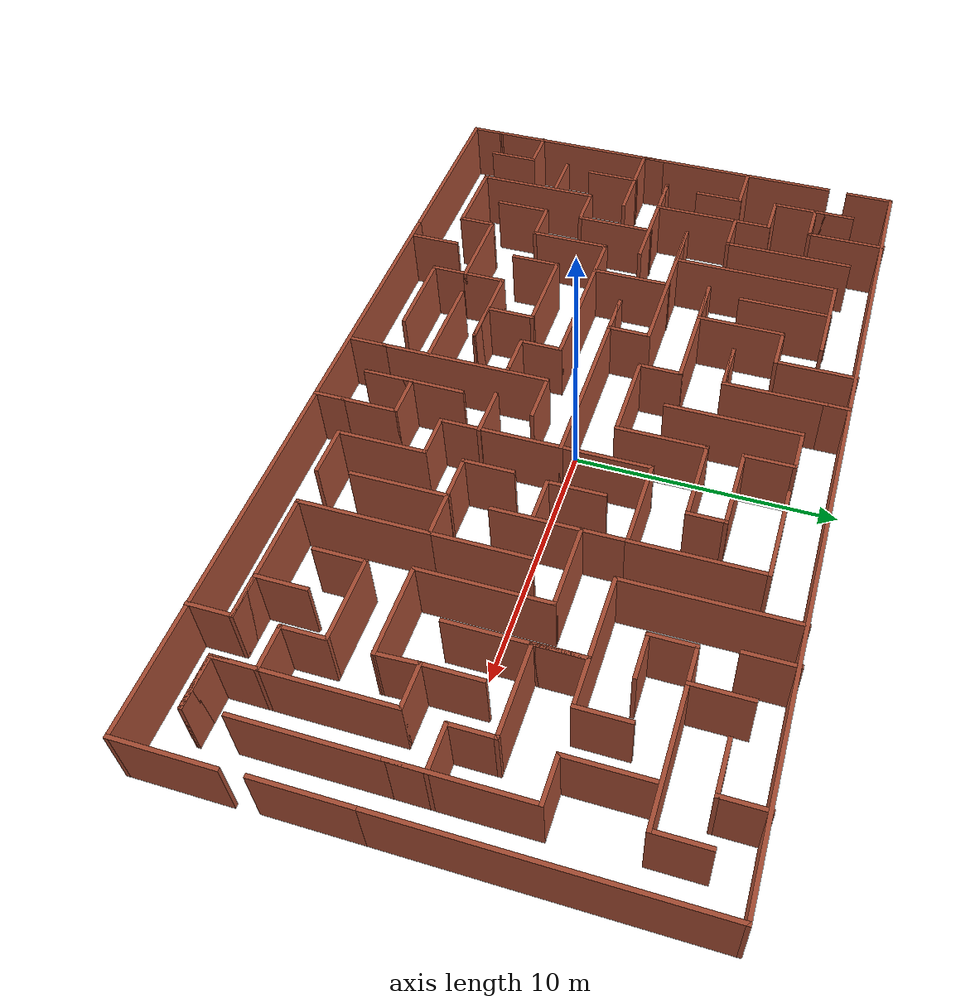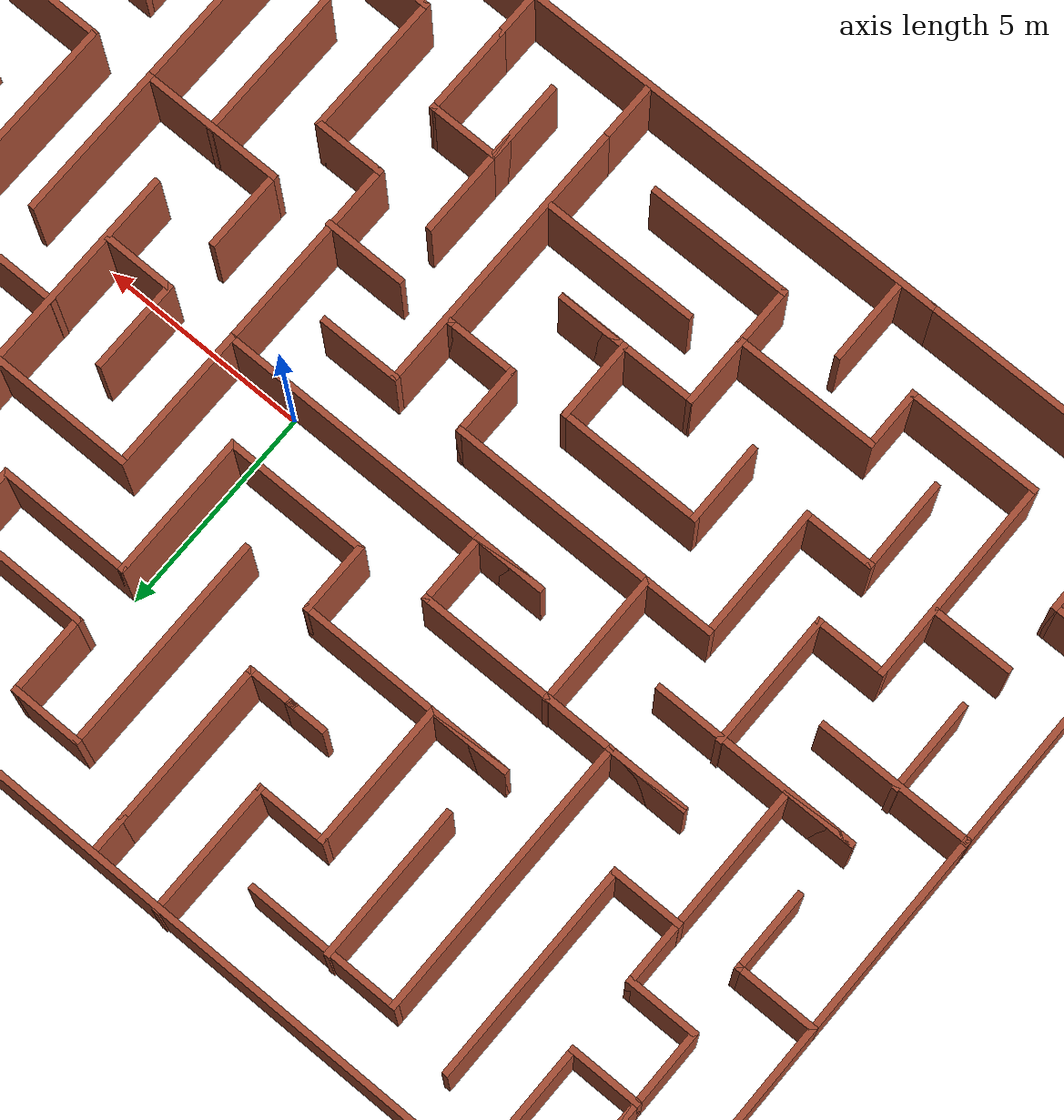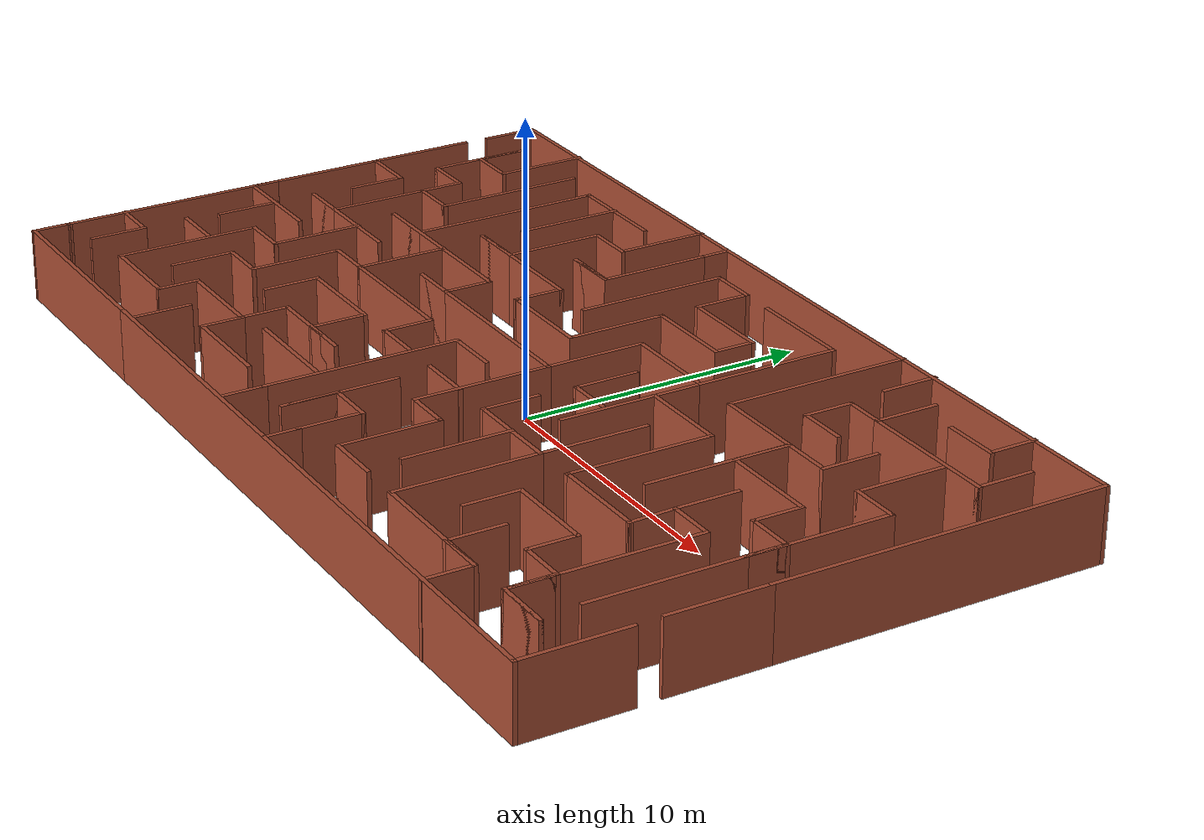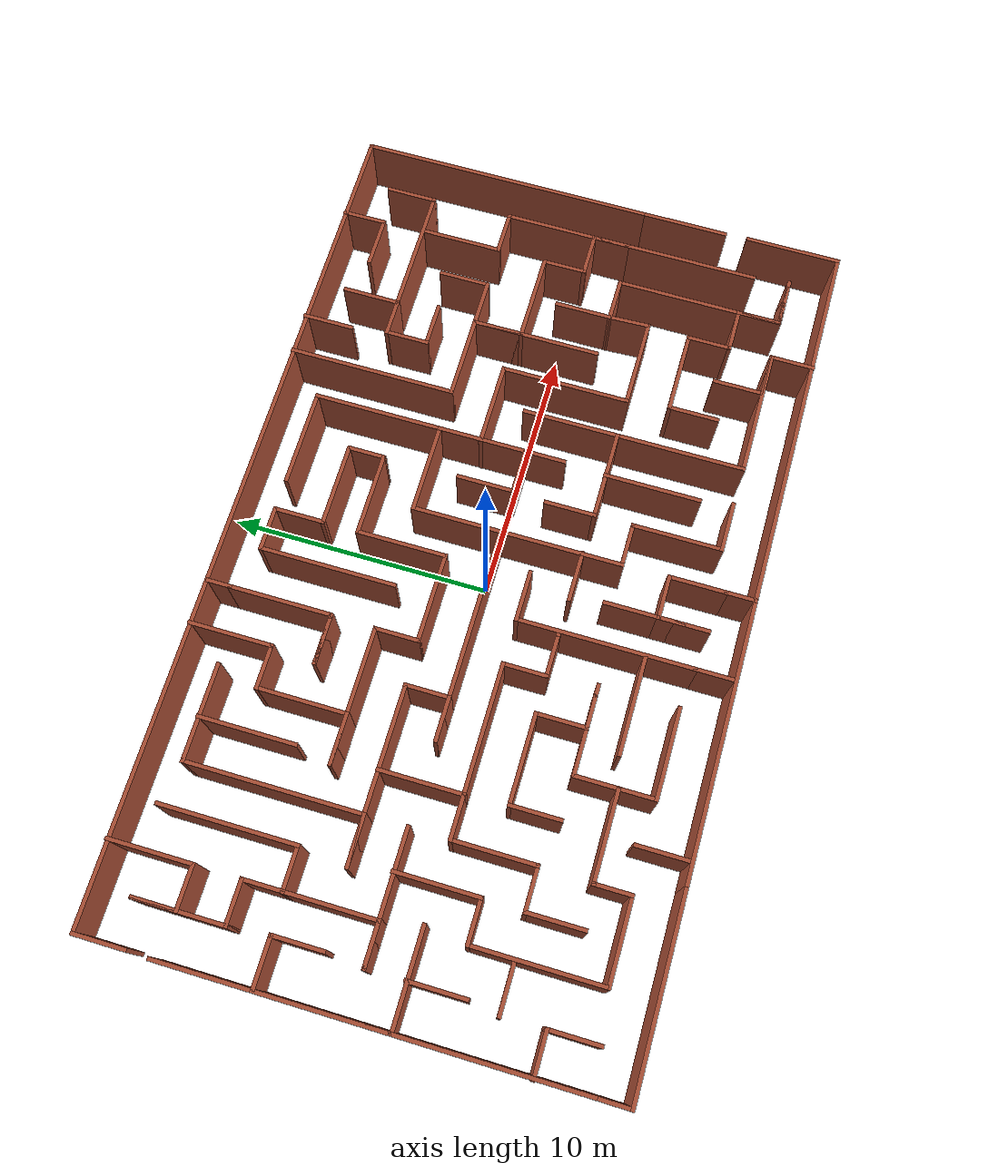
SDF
<?xml version='1.0'?>
<sdf version='1.7'>
  <model name='model_maze_2'>
    <pose>-0.012722 -0.022539 0 0 -0 0</pose>
    <link name='Wall_0'>
      <collision name='Wall_0_Collision'>
        <geometry>
          <box>
            <size>2 0.15 2.5</size>
          </box>
        </geometry>
        <pose>0 0 1.25 0 -0 0</pose>
      </collision>
      <visual name='Wall_0_Visual'>
        <pose>0 0 1.25 0 -0 0</pose>
        <geometry>
          <box>
            <size>2 0.15 2.5</size>
          </box>
        </geometry>
        <material>
          <script>
            <uri>file://media/materials/scripts/gazebo.material</uri>
            <name>Gazebo/Bricks</name>
          </script>
          <ambient>1 1 1 1</ambient>
        </material>
        <meta>
          <layer>0</layer>
        </meta>
      </visual>
      <pose>-16.1592 8.67968 0 0 -0 1.5708</pose>
    </link>
    <link name='Wall_1'>
      <collision name='Wall_1_Collision'>
        <geometry>
          <box>
            <size>32.5 0.15 2.5</size>
          </box>
        </geometry>
        <pose>0 0 1.25 0 -0 0</pose>
      </collision>
      <visual name='Wall_1_Visual'>
        <pose>0 0 1.25 0 -0 0</pose>
        <geometry>
          <box>
            <size>32.5 0.15 2.5</size>
          </box>
        </geometry>
        <material>
          <script>
            <uri>file://media/materials/scripts/gazebo.material</uri>
            <name>Gazebo/Bricks</name>
          </script>
          <ambient>1 1 1 1</ambient>
        </material>
        <meta>
          <layer>0</layer>
        </meta>
      </visual>
      <pose>0.01583 9.60468 0 0 -0 0</pose>
    </link>
    <link name='Wall_10'>
      <collision name='Wall_10_Collision'>
        <geometry>
          <box>
            <size>1.75 0.15 2.5</size>
          </box>
        </geometry>
        <pose>0 0 1.25 0 -0 0</pose>
      </collision>
      <visual name='Wall_10_Visual'>
        <pose>0 0 1.25 0 -0 0</pose>
        <geometry>
          <box>
            <size>1.75 0.15 2.5</size>
          </box>
        </geometry>
        <material>
          <script>
            <uri>file://media/materials/scripts/gazebo.material</uri>
            <name>Gazebo/Bricks</name>
          </script>
          <ambient>1 1 1 1</ambient>
        </material>
        <meta>
          <layer>0</layer>
        </meta>
      </visual>
      <pose>-13.6978 -0.048612 0 0 -0 3.14159</pose>
    </link>
    <link name='Wall_100'>
      <collision name='Wall_100_Collision'>
        <geometry>
          <box>
            <size>1.75 0.15 2.5</size>
          </box>
        </geometry>
        <pose>0 0 1.25 0 -0 0</pose>
      </collision>
      <visual name='Wall_100_Visual'>
        <pose>0 0 1.25 0 -0 0</pose>
        <geometry>
          <box>
            <size>1.75 0.15 2.5</size>
          </box>
        </geometry>
        <material>
          <script>
            <uri>file://media/materials/scripts/gazebo.material</uri>
            <name>Gazebo/Bricks</name>
          </script>
          <ambient>1 1 1 1</ambient>
        </material>
        <meta>
          <layer>0</layer>
        </meta>
      </visual>
      <pose>11.303 -5.61671 0 0 -0 1.5708</pose>
    </link>
    <link name='Wall_101'>
      <collision name='Wall_101_Collision'>
        <geometry>
          <box>
            <size>3.25 0.15 2.5</size>
          </box>
        </geometry>
        <pose>0 0 1.25 0 -0 0</pose>
      </collision>
      <visual name='Wall_101_Visual'>
        <pose>0 0 1.25 0 -0 0</pose>
        <geometry>
          <box>
            <size>3.25 0.15 2.5</size>
          </box>
        </geometry>
        <material>
          <script>
            <uri>file://media/materials/scripts/gazebo.material</uri>
            <name>Gazebo/Bricks</name>
          </script>
          <ambient>1 1 1 1</ambient>
        </material>
        <meta>
          <layer>0</layer>
        </meta>
      </visual>
      <pose>9.75296 -4.81671 0 0 -0 3.14159</pose>
    </link>
    <link name='Wall_102'>
      <collision name='Wall_102_Collision'>
        <geometry>
          <box>
            <size>2 0.15 2.5</size>
          </box>
        </geometry>
        <pose>0 0 1.25 0 -0 0</pose>
      </collision>
      <visual name='Wall_102_Visual'>
        <pose>0 0 1.25 0 -0 0</pose>
        <geometry>
          <box>
            <size>2 0.15 2.5</size>
          </box>
        </geometry>
        <material>
          <script>
            <uri>file://media/materials/scripts/gazebo.material</uri>
            <name>Gazebo/Bricks</name>
          </script>
          <ambient>1 1 1 1</ambient>
        </material>
        <meta>
          <layer>0</layer>
        </meta>
      </visual>
      <pose>8.20296 -5.74171 0 0 -0 -1.5708</pose>
    </link>
    <link name='Wall_104'>
      <collision name='Wall_104_Collision'>
        <geometry>
          <box>
            <size>5.25 0.15 2.5</size>
          </box>
        </geometry>
        <pose>0 0 1.25 0 -0 0</pose>
      </collision>
      <visual name='Wall_104_Visual'>
        <pose>0 0 1.25 0 -0 0</pose>
        <geometry>
          <box>
            <size>5.25 0.15 2.5</size>
          </box>
        </geometry>
        <material>
          <script>
            <uri>file://media/materials/scripts/gazebo.material</uri>
            <name>Gazebo/Bricks</name>
          </script>
          <ambient>1 1 1 1</ambient>
        </material>
        <meta>
          <layer>0</layer>
        </meta>
      </visual>
      <pose>14.587 -4.07531 0 0 -0 -1.5708</pose>
    </link>
    <link name='Wall_106'>
      <collision name='Wall_106_Collision'>
        <geometry>
          <box>
            <size>3.5 0.15 2.5</size>
          </box>
        </geometry>
        <pose>0 0 1.25 0 -0 0</pose>
      </collision>
      <visual name='Wall_106_Visual'>
        <pose>0 0 1.25 0 -0 0</pose>
        <geometry>
          <box>
            <size>3.5 0.15 2.5</size>
          </box>
        </geometry>
        <material>
          <script>
            <uri>file://media/materials/scripts/gazebo.material</uri>
            <name>Gazebo/Bricks</name>
          </script>
          <ambient>1 1 1 1</ambient>
        </material>
        <meta>
          <layer>0</layer>
        </meta>
      </visual>
      <pose>16.1908 -3.42032 0 0 -0 -1.5708</pose>
    </link>
    <link name='Wall_108'>
      <collision name='Wall_108_Collision'>
        <geometry>
          <box>
            <size>4.75 0.15 2.5</size>
          </box>
        </geometry>
        <pose>0 0 1.25 0 -0 0</pose>
      </collision>
      <visual name='Wall_108_Visual'>
        <pose>0 0 1.25 0 -0 0</pose>
        <geometry>
          <box>
            <size>4.75 0.15 2.5</size>
          </box>
        </geometry>
        <material>
          <script>
            <uri>file://media/materials/scripts/gazebo.material</uri>
            <name>Gazebo/Bricks</name>
          </script>
          <ambient>1 1 1 1</ambient>
        </material>
        <meta>
          <layer>0</layer>
        </meta>
      </visual>
      <pose>1.57577 -2.37523 0 0 -0 -1.5708</pose>
    </link>
    <link name='Wall_109'>
      <collision name='Wall_109_Collision'>
        <geometry>
          <box>
            <size>1.75 0.15 2.5</size>
          </box>
        </geometry>
        <pose>0 0 1.25 0 -0 0</pose>
      </collision>
      <visual name='Wall_109_Visual'>
        <pose>0 0 1.25 0 -0 0</pose>
        <geometry>
          <box>
            <size>1.75 0.15 2.5</size>
          </box>
        </geometry>
        <material>
          <script>
            <uri>file://media/materials/scripts/gazebo.material</uri>
            <name>Gazebo/Bricks</name>
          </script>
          <ambient>1 1 1 1</ambient>
        </material>
        <meta>
          <layer>0</layer>
        </meta>
      </visual>
      <pose>2.37577 -4.67523 0 0 -0 0</pose>
    </link>
    <link name='Wall_11'>
      <collision name='Wall_11_Collision'>
        <geometry>
          <box>
            <size>5 0.15 2.5</size>
          </box>
        </geometry>
        <pose>0 0 1.25 0 -0 0</pose>
      </collision>
      <visual name='Wall_11_Visual'>
        <pose>0 0 1.25 0 -0 0</pose>
        <geometry>
          <box>
            <size>5 0.15 2.5</size>
          </box>
        </geometry>
        <material>
          <script>
            <uri>file://media/materials/scripts/gazebo.material</uri>
            <name>Gazebo/Bricks</name>
          </script>
          <ambient>1 1 1 1</ambient>
        </material>
        <meta>
          <layer>0</layer>
        </meta>
      </visual>
      <pose>-12.0728 -0.048612 0 0 -0 0</pose>
    </link>
    <link name='Wall_110'>
      <collision name='Wall_110_Collision'>
        <geometry>
          <box>
            <size>3.5 0.15 2.5</size>
          </box>
        </geometry>
        <pose>0 0 1.25 0 -0 0</pose>
      </collision>
      <visual name='Wall_110_Visual'>
        <pose>0 0 1.25 0 -0 0</pose>
        <geometry>
          <box>
            <size>3.5 0.15 2.5</size>
          </box>
        </geometry>
        <material>
          <script>
            <uri>file://media/materials/scripts/gazebo.material</uri>
            <name>Gazebo/Bricks</name>
          </script>
          <ambient>1 1 1 1</ambient>
        </material>
        <meta>
          <layer>0</layer>
        </meta>
      </visual>
      <pose>3.17577 -6.35023 0 0 -0 -1.5708</pose>
    </link>
    <link name='Wall_111'>
      <collision name='Wall_111_Collision'>
        <geometry>
          <box>
            <size>2 0.15 2.5</size>
          </box>
        </geometry>
        <pose>0 0 1.25 0 -0 0</pose>
      </collision>
      <visual name='Wall_111_Visual'>
        <pose>0 0 1.25 0 -0 0</pose>
        <geometry>
          <box>
            <size>2 0.15 2.5</size>
          </box>
        </geometry>
        <material>
          <script>
            <uri>file://media/materials/scripts/gazebo.material</uri>
            <name>Gazebo/Bricks</name>
          </script>
          <ambient>1 1 1 1</ambient>
        </material>
        <meta>
          <layer>0</layer>
        </meta>
      </visual>
      <pose>4.10077 -8.02523 0 0 -0 0</pose>
    </link>
    <link name='Wall_113'>
      <collision name='Wall_113_Collision'>
        <geometry>
          <box>
            <size>3.75 0.15 2.5</size>
          </box>
        </geometry>
        <pose>0 0 1.25 0 -0 0</pose>
      </collision>
      <visual name='Wall_113_Visual'>
        <pose>0 0 1.25 0 -0 0</pose>
        <geometry>
          <box>
            <size>3.75 0.15 2.5</size>
          </box>
        </geometry>
        <material>
          <script>
            <uri>file://media/materials/scripts/gazebo.material</uri>
            <name>Gazebo/Bricks</name>
          </script>
          <ambient>1 1 1 1</ambient>
        </material>
        <meta>
          <layer>0</layer>
        </meta>
      </visual>
      <pose>6.51493 -1.41297 0 0 -0 -1.5708</pose>
    </link>
    <link name='Wall_114'>
      <collision name='Wall_114_Collision'>
        <geometry>
          <box>
            <size>3.5 0.15 2.5</size>
          </box>
        </geometry>
        <pose>0 0 1.25 0 -0 0</pose>
      </collision>
      <visual name='Wall_114_Visual'>
        <pose>0 0 1.25 0 -0 0</pose>
        <geometry>
          <box>
            <size>3.5 0.15 2.5</size>
          </box>
        </geometry>
        <material>
          <script>
            <uri>file://media/materials/scripts/gazebo.material</uri>
            <name>Gazebo/Bricks</name>
          </script>
          <ambient>1 1 1 1</ambient>
        </material>
        <meta>
          <layer>0</layer>
        </meta>
      </visual>
      <pose>4.83993 -3.21297 0 0 -0 3.14159</pose>
    </link>
    <link name='Wall_115'>
      <collision name='Wall_115_Collision'>
        <geometry>
          <box>
            <size>2 0.15 2.5</size>
          </box>
        </geometry>
        <pose>0 0 1.25 0 -0 0</pose>
      </collision>
      <visual name='Wall_115_Visual'>
        <pose>0 0 1.25 0 -0 0</pose>
        <geometry>
          <box>
            <size>2 0.15 2.5</size>
          </box>
        </geometry>
        <material>
          <script>
            <uri>file://media/materials/scripts/gazebo.material</uri>
            <name>Gazebo/Bricks</name>
          </script>
          <ambient>1 1 1 1</ambient>
        </material>
        <meta>
          <layer>0</layer>
        </meta>
      </visual>
      <pose>3.16493 -2.28797 0 0 -0 1.5708</pose>
    </link>
    <link name='Wall_117'>
      <collision name='Wall_117_Collision'>
        <geometry>
          <box>
            <size>5 0.15 2.5</size>
          </box>
        </geometry>
        <pose>0 0 1.25 0 -0 0</pose>
      </collision>
      <visual name='Wall_117_Visual'>
        <pose>0 0 1.25 0 -0 0</pose>
        <geometry>
          <box>
            <size>5 0.15 2.5</size>
          </box>
        </geometry>
        <material>
          <script>
            <uri>file://media/materials/scripts/gazebo.material</uri>
            <name>Gazebo/Bricks</name>
          </script>
          <ambient>1 1 1 1</ambient>
        </material>
        <meta>
          <layer>0</layer>
        </meta>
      </visual>
      <pose>6.51493 -5.63797 0 0 -0 -1.5708</pose>
    </link>
    <link name='Wall_118'>
      <collision name='Wall_118_Collision'>
        <geometry>
          <box>
            <size>5 0.15 2.5</size>
          </box>
        </geometry>
        <pose>0 0 1.25 0 -0 0</pose>
      </collision>
      <visual name='Wall_118_Visual'>
        <pose>0 0 1.25 0 -0 0</pose>
        <geometry>
          <box>
            <size>5 0.15 2.5</size>
          </box>
        </geometry>
        <material>
          <script>
            <uri>file://media/materials/scripts/gazebo.material</uri>
            <name>Gazebo/Bricks</name>
          </script>
          <ambient>1 1 1 1</ambient>
        </material>
        <meta>
          <layer>0</layer>
        </meta>
      </visual>
      <pose>8.93993 -8.06297 0 0 -0 0</pose>
    </link>
    <link name='Wall_119'>
      <collision name='Wall_119_Collision'>
        <geometry>
          <box>
            <size>1.75 0.15 2.5</size>
          </box>
        </geometry>
        <pose>0 0 1.25 0 -0 0</pose>
      </collision>
      <visual name='Wall_119_Visual'>
        <pose>0 0 1.25 0 -0 0</pose>
        <geometry>
          <box>
            <size>1.75 0.15 2.5</size>
          </box>
        </geometry>
        <material>
          <script>
            <uri>file://media/materials/scripts/gazebo.material</uri>
            <name>Gazebo/Bricks</name>
          </script>
          <ambient>1 1 1 1</ambient>
        </material>
        <meta>
          <layer>0</layer>
        </meta>
      </visual>
      <pose>10.5649 -8.06297 0 0 -0 3.14159</pose>
    </link>
    <link name='Wall_120'>
      <collision name='Wall_120_Collision'>
        <geometry>
          <box>
            <size>2 0.15 2.5</size>
          </box>
        </geometry>
        <pose>0 0 1.25 0 -0 0</pose>
      </collision>
      <visual name='Wall_120_Visual'>
        <pose>0 0 1.25 0 -0 0</pose>
        <geometry>
          <box>
            <size>2 0.15 2.5</size>
          </box>
        </geometry>
        <material>
          <script>
            <uri>file://media/materials/scripts/gazebo.material</uri>
            <name>Gazebo/Bricks</name>
          </script>
          <ambient>1 1 1 1</ambient>
        </material>
        <meta>
          <layer>0</layer>
        </meta>
      </visual>
      <pose>9.76493 -7.13797 0 0 -0 1.5708</pose>
    </link>
    <link name='Wall_122'>
      <collision name='Wall_122_Collision'>
        <geometry>
          <box>
            <size>3.75 0.15 2.5</size>
          </box>
        </geometry>
        <pose>0 0 1.25 0 -0 0</pose>
      </collision>
      <visual name='Wall_122_Visual'>
        <pose>0 0 1.25 0 -0 0</pose>
        <geometry>
          <box>
            <size>3.75 0.15 2.5</size>
          </box>
        </geometry>
        <material>
          <script>
            <uri>file://media/materials/scripts/gazebo.material</uri>
            <name>Gazebo/Bricks</name>
          </script>
          <ambient>1 1 1 1</ambient>
        </material>
        <meta>
          <layer>0</layer>
        </meta>
      </visual>
      <pose>4.82639 -4.99822 0 0 -0 -1.5708</pose>
    </link>
    <link name='Wall_124'>
      <collision name='Wall_124_Collision'>
        <geometry>
          <box>
            <size>2 0.15 2.5</size>
          </box>
        </geometry>
        <pose>0 0 1.25 0 -0 0</pose>
      </collision>
      <visual name='Wall_124_Visual'>
        <pose>0 0 1.25 0 -0 0</pose>
        <geometry>
          <box>
            <size>2 0.15 2.5</size>
          </box>
        </geometry>
        <material>
          <script>
            <uri>file://media/materials/scripts/gazebo.material</uri>
            <name>Gazebo/Bricks</name>
          </script>
          <ambient>1 1 1 1</ambient>
        </material>
        <meta>
          <layer>0</layer>
        </meta>
      </visual>
      <pose>0.686237 -3.17508 0 0 -0 3.14159</pose>
    </link>
    <link name='Wall_126'>
      <collision name='Wall_126_Collision'>
        <geometry>
          <box>
            <size>2 0.15 2.5</size>
          </box>
        </geometry>
        <pose>0 0 1.25 0 -0 0</pose>
      </collision>
      <visual name='Wall_126_Visual'>
        <pose>0 0 1.25 0 -0 0</pose>
        <geometry>
          <box>
            <size>2 0.15 2.5</size>
          </box>
        </geometry>
        <material>
          <script>
            <uri>file://media/materials/scripts/gazebo.material</uri>
            <name>Gazebo/Bricks</name>
          </script>
          <ambient>1 1 1 1</ambient>
        </material>
        <meta>
          <layer>0</layer>
        </meta>
      </visual>
      <pose>-0.562816 -1.55594 0 0 -0 3.14159</pose>
    </link>
    <link name='Wall_127'>
      <collision name='Wall_127_Collision'>
        <geometry>
          <box>
            <size>6.75 0.15 2.5</size>
          </box>
        </geometry>
        <pose>0 0 1.25 0 -0 0</pose>
      </collision>
      <visual name='Wall_127_Visual'>
        <pose>0 0 1.25 0 -0 0</pose>
        <geometry>
          <box>
            <size>6.75 0.15 2.5</size>
          </box>
        </geometry>
        <material>
          <script>
            <uri>file://media/materials/scripts/gazebo.material</uri>
            <name>Gazebo/Bricks</name>
          </script>
          <ambient>1 1 1 1</ambient>
        </material>
        <meta>
          <layer>0</layer>
        </meta>
      </visual>
      <pose>-1.48782 -4.85594 0 0 -0 -1.5708</pose>
    </link>
    <link name='Wall_13'>
      <collision name='Wall_13_Collision'>
        <geometry>
          <box>
            <size>3.75 0.15 2.5</size>
          </box>
        </geometry>
        <pose>0 0 1.25 0 -0 0</pose>
      </collision>
      <visual name='Wall_13_Visual'>
        <pose>0 0 1.25 0 -0 0</pose>
        <geometry>
          <box>
            <size>3.75 0.15 2.5</size>
          </box>
        </geometry>
        <material>
          <script>
            <uri>file://media/materials/scripts/gazebo.material</uri>
            <name>Gazebo/Bricks</name>
          </script>
          <ambient>1 1 1 1</ambient>
        </material>
        <meta>
          <layer>0</layer>
        </meta>
      </visual>
      <pose>-16.2054 5.05258 0 0 -0 -1.5708</pose>
    </link>
    <link name='Wall_130'>
      <collision name='Wall_130_Collision'>
        <geometry>
          <box>
            <size>1.75 0.15 2.5</size>
          </box>
        </geometry>
        <pose>0 0 1.25 0 -0 0</pose>
      </collision>
      <visual name='Wall_130_Visual'>
        <pose>0 0 1.25 0 -0 0</pose>
        <geometry>
          <box>
            <size>1.75 0.15 2.5</size>
          </box>
        </geometry>
        <material>
          <script>
            <uri>file://media/materials/scripts/gazebo.material</uri>
            <name>Gazebo/Bricks</name>
          </script>
          <ambient>1 1 1 1</ambient>
        </material>
        <meta>
          <layer>0</layer>
        </meta>
      </visual>
      <pose>-8.86181 -1.55587 0 0 -0 3.14159</pose>
    </link>
    <link name='Wall_131'>
      <collision name='Wall_131_Collision'>
        <geometry>
          <box>
            <size>3.25 0.15 2.5</size>
          </box>
        </geometry>
        <pose>0 0 1.25 0 -0 0</pose>
      </collision>
      <visual name='Wall_131_Visual'>
        <pose>0 0 1.25 0 -0 0</pose>
        <geometry>
          <box>
            <size>3.25 0.15 2.5</size>
          </box>
        </geometry>
        <material>
          <script>
            <uri>file://media/materials/scripts/gazebo.material</uri>
            <name>Gazebo/Bricks</name>
          </script>
          <ambient>1 1 1 1</ambient>
        </material>
        <meta>
          <layer>0</layer>
        </meta>
      </visual>
      <pose>-9.66181 -3.10587 0 0 -0 -1.5708</pose>
    </link>
    <link name='Wall_132'>
      <collision name='Wall_132_Collision'>
        <geometry>
          <box>
            <size>1.75 0.15 2.5</size>
          </box>
        </geometry>
        <pose>0 0 1.25 0 -0 0</pose>
      </collision>
      <visual name='Wall_132_Visual'>
        <pose>0 0 1.25 0 -0 0</pose>
        <geometry>
          <box>
            <size>1.75 0.15 2.5</size>
          </box>
        </geometry>
        <material>
          <script>
            <uri>file://media/materials/scripts/gazebo.material</uri>
            <name>Gazebo/Bricks</name>
          </script>
          <ambient>1 1 1 1</ambient>
        </material>
        <meta>
          <layer>0</layer>
        </meta>
      </visual>
      <pose>-10.4618 -4.65587 0 0 -0 3.14159</pose>
    </link>
    <link name='Wall_133'>
      <collision name='Wall_133_Collision'>
        <geometry>
          <box>
            <size>2.25 0.15 2.5</size>
          </box>
        </geometry>
        <pose>0 0 1.25 0 -0 0</pose>
      </collision>
      <visual name='Wall_133_Visual'>
        <pose>0 0 1.25 0 -0 0</pose>
        <geometry>
          <box>
            <size>2.25 0.15 2.5</size>
          </box>
        </geometry>
        <material>
          <script>
            <uri>file://media/materials/scripts/gazebo.material</uri>
            <name>Gazebo/Bricks</name>
          </script>
          <ambient>1 1 1 1</ambient>
        </material>
        <meta>
          <layer>0</layer>
        </meta>
      </visual>
      <pose>-11.2618 -5.70587 0 0 -0 -1.5708</pose>
    </link>
    <link name='Wall_135'>
      <collision name='Wall_135_Collision'>
        <geometry>
          <box>
            <size>5 0.15 2.5</size>
          </box>
        </geometry>
        <pose>0 0 1.25 0 -0 0</pose>
      </collision>
      <visual name='Wall_135_Visual'>
        <pose>0 0 1.25 0 -0 0</pose>
        <geometry>
          <box>
            <size>5 0.15 2.5</size>
          </box>
        </geometry>
        <material>
          <script>
            <uri>file://media/materials/scripts/gazebo.material</uri>
            <name>Gazebo/Bricks</name>
          </script>
          <ambient>1 1 1 1</ambient>
        </material>
        <meta>
          <layer>0</layer>
        </meta>
      </visual>
      <pose>-5.63681 -1.55587 0 0 -0 0</pose>
    </link>
    <link name='Wall_136'>
      <collision name='Wall_136_Collision'>
        <geometry>
          <box>
            <size>1.75 0.15 2.5</size>
          </box>
        </geometry>
        <pose>0 0 1.25 0 -0 0</pose>
      </collision>
      <visual name='Wall_136_Visual'>
        <pose>0 0 1.25 0 -0 0</pose>
        <geometry>
          <box>
            <size>1.75 0.15 2.5</size>
          </box>
        </geometry>
        <material>
          <script>
            <uri>file://media/materials/scripts/gazebo.material</uri>
            <name>Gazebo/Bricks</name>
          </script>
          <ambient>1 1 1 1</ambient>
        </material>
        <meta>
          <layer>0</layer>
        </meta>
      </visual>
      <pose>-3.21181 -2.35587 0 0 -0 -1.5708</pose>
    </link>
    <link name='Wall_137'>
      <collision name='Wall_137_Collision'>
        <geometry>
          <box>
            <size>1.75 0.15 2.5</size>
          </box>
        </geometry>
        <pose>0 0 1.25 0 -0 0</pose>
      </collision>
      <visual name='Wall_137_Visual'>
        <pose>0 0 1.25 0 -0 0</pose>
        <geometry>
          <box>
            <size>1.75 0.15 2.5</size>
          </box>
        </geometry>
        <material>
          <script>
            <uri>file://media/materials/scripts/gazebo.material</uri>
            <name>Gazebo/Bricks</name>
          </script>
          <ambient>1 1 1 1</ambient>
        </material>
        <meta>
          <layer>0</layer>
        </meta>
      </visual>
      <pose>-2.41181 -3.15587 0 0 -0 0</pose>
    </link>
    <link name='Wall_138'>
      <collision name='Wall_138_Collision'>
        <geometry>
          <box>
            <size>0.15 0.15 2.5</size>
          </box>
        </geometry>
        <pose>0 0 1.25 0 -0 0</pose>
      </collision>
      <visual name='Wall_138_Visual'>
        <pose>0 0 1.25 0 -0 0</pose>
        <geometry>
          <box>
            <size>0.15 0.15 2.5</size>
          </box>
        </geometry>
        <material>
          <script>
            <uri>file://media/materials/scripts/gazebo.material</uri>
            <name>Gazebo/Bricks</name>
          </script>
          <ambient>1 1 1 1</ambient>
        </material>
        <meta>
          <layer>0</layer>
        </meta>
      </visual>
      <pose>-1.61181 -3.15587 0 0 -0 0</pose>
    </link>
    <link name='Wall_14'>
      <collision name='Wall_14_Collision'>
        <geometry>
          <box>
            <size>2 0.15 2.5</size>
          </box>
        </geometry>
        <pose>0 0 1.25 0 -0 0</pose>
      </collision>
      <visual name='Wall_14_Visual'>
        <pose>0 0 1.25 0 -0 0</pose>
        <geometry>
          <box>
            <size>2 0.15 2.5</size>
          </box>
        </geometry>
        <material>
          <script>
            <uri>file://media/materials/scripts/gazebo.material</uri>
            <name>Gazebo/Bricks</name>
          </script>
          <ambient>1 1 1 1</ambient>
        </material>
        <meta>
          <layer>0</layer>
        </meta>
      </visual>
      <pose>-15.2804 3.25258 0 0 -0 0</pose>
    </link>
    <link name='Wall_140'>
      <collision name='Wall_140_Collision'>
        <geometry>
          <box>
            <size>3.25 0.15 2.5</size>
          </box>
        </geometry>
        <pose>0 0 1.25 0 -0 0</pose>
      </collision>
      <visual name='Wall_140_Visual'>
        <pose>0 0 1.25 0 -0 0</pose>
        <geometry>
          <box>
            <size>3.25 0.15 2.5</size>
          </box>
        </geometry>
        <material>
          <script>
            <uri>file://media/materials/scripts/gazebo.material</uri>
            <name>Gazebo/Bricks</name>
          </script>
          <ambient>1 1 1 1</ambient>
        </material>
        <meta>
          <layer>0</layer>
        </meta>
      </visual>
      <pose>-11.2176 -1.56101 0 0 -0 -1.5708</pose>
    </link>
    <link name='Wall_141'>
      <collision name='Wall_141_Collision'>
        <geometry>
          <box>
            <size>1.75 0.15 2.5</size>
          </box>
        </geometry>
        <pose>0 0 1.25 0 -0 0</pose>
      </collision>
      <visual name='Wall_141_Visual'>
        <pose>0 0 1.25 0 -0 0</pose>
        <geometry>
          <box>
            <size>1.75 0.15 2.5</size>
          </box>
        </geometry>
        <material>
          <script>
            <uri>file://media/materials/scripts/gazebo.material</uri>
            <name>Gazebo/Bricks</name>
          </script>
          <ambient>1 1 1 1</ambient>
        </material>
        <meta>
          <layer>0</layer>
        </meta>
      </visual>
      <pose>-12.0176 -3.11101 0 0 -0 3.14159</pose>
    </link>
    <link name='Wall_142'>
      <collision name='Wall_142_Collision'>
        <geometry>
          <box>
            <size>5 0.15 2.5</size>
          </box>
        </geometry>
        <pose>0 0 1.25 0 -0 0</pose>
      </collision>
      <visual name='Wall_142_Visual'>
        <pose>0 0 1.25 0 -0 0</pose>
        <geometry>
          <box>
            <size>5 0.15 2.5</size>
          </box>
        </geometry>
        <material>
          <script>
            <uri>file://media/materials/scripts/gazebo.material</uri>
            <name>Gazebo/Bricks</name>
          </script>
          <ambient>1 1 1 1</ambient>
        </material>
        <meta>
          <layer>0</layer>
        </meta>
      </visual>
      <pose>-12.8176 -5.53601 0 0 -0 -1.5708</pose>
    </link>
    <link name='Wall_143'>
      <collision name='Wall_143_Collision'>
        <geometry>
          <box>
            <size>3.25 0.15 2.5</size>
          </box>
        </geometry>
        <pose>0 0 1.25 0 -0 0</pose>
      </collision>
      <visual name='Wall_143_Visual'>
        <pose>0 0 1.25 0 -0 0</pose>
        <geometry>
          <box>
            <size>3.25 0.15 2.5</size>
          </box>
        </geometry>
        <material>
          <script>
            <uri>file://media/materials/scripts/gazebo.material</uri>
            <name>Gazebo/Bricks</name>
          </script>
          <ambient>1 1 1 1</ambient>
        </material>
        <meta>
          <layer>0</layer>
        </meta>
      </visual>
      <pose>-11.2676 -7.96101 0 0 -0 0</pose>
    </link>
    <link name='Wall_144'>
      <collision name='Wall_144_Collision'>
        <geometry>
          <box>
            <size>1.5 0.15 2.5</size>
          </box>
        </geometry>
        <pose>0 0 1.25 0 -0 0</pose>
      </collision>
      <visual name='Wall_144_Visual'>
        <pose>0 0 1.25 0 -0 0</pose>
        <geometry>
          <box>
            <size>1.5 0.15 2.5</size>
          </box>
        </geometry>
        <material>
          <script>
            <uri>file://media/materials/scripts/gazebo.material</uri>
            <name>Gazebo/Bricks</name>
          </script>
          <ambient>1 1 1 1</ambient>
        </material>
        <meta>
          <layer>0</layer>
        </meta>
      </visual>
      <pose>-9.71757 -7.28601 0 0 -0 1.5708</pose>
    </link>
    <link name='Wall_145'>
      <collision name='Wall_145_Collision'>
        <geometry>
          <box>
            <size>3.5 0.15 2.5</size>
          </box>
        </geometry>
        <pose>0 0 1.25 0 -0 0</pose>
      </collision>
      <visual name='Wall_145_Visual'>
        <pose>0 0 1.25 0 -0 0</pose>
        <geometry>
          <box>
            <size>3.5 0.15 2.5</size>
          </box>
        </geometry>
        <material>
          <script>
            <uri>file://media/materials/scripts/gazebo.material</uri>
            <name>Gazebo/Bricks</name>
          </script>
          <ambient>1 1 1 1</ambient>
        </material>
        <meta>
          <layer>0</layer>
        </meta>
      </visual>
      <pose>-8.04257 -6.61101 0 0 -0 0</pose>
    </link>
    <link name='Wall_146'>
      <collision name='Wall_146_Collision'>
        <geometry>
          <box>
            <size>1.75 0.15 2.5</size>
          </box>
        </geometry>
        <pose>0 0 1.25 0 -0 0</pose>
      </collision>
      <visual name='Wall_146_Visual'>
        <pose>0 0 1.25 0 -0 0</pose>
        <geometry>
          <box>
            <size>1.75 0.15 2.5</size>
          </box>
        </geometry>
        <material>
          <script>
            <uri>file://media/materials/scripts/gazebo.material</uri>
            <name>Gazebo/Bricks</name>
          </script>
          <ambient>1 1 1 1</ambient>
        </material>
        <meta>
          <layer>0</layer>
        </meta>
      </visual>
      <pose>-6.36757 -5.81101 0 0 -0 1.5708</pose>
    </link>
    <link name='Wall_147'>
      <collision name='Wall_147_Collision'>
        <geometry>
          <box>
            <size>3.5 0.15 2.5</size>
          </box>
        </geometry>
        <pose>0 0 1.25 0 -0 0</pose>
      </collision>
      <visual name='Wall_147_Visual'>
        <pose>0 0 1.25 0 -0 0</pose>
        <geometry>
          <box>
            <size>3.5 0.15 2.5</size>
          </box>
        </geometry>
        <material>
          <script>
            <uri>file://media/materials/scripts/gazebo.material</uri>
            <name>Gazebo/Bricks</name>
          </script>
          <ambient>1 1 1 1</ambient>
        </material>
        <meta>
          <layer>0</layer>
        </meta>
      </visual>
      <pose>-4.69257 -5.01101 0 0 -0 0</pose>
    </link>
    <link name='Wall_148'>
      <collision name='Wall_148_Collision'>
        <geometry>
          <box>
            <size>1.75 0.15 2.5</size>
          </box>
        </geometry>
        <pose>0 0 1.25 0 -0 0</pose>
      </collision>
      <visual name='Wall_148_Visual'>
        <pose>0 0 1.25 0 -0 0</pose>
        <geometry>
          <box>
            <size>1.75 0.15 2.5</size>
          </box>
        </geometry>
        <material>
          <script>
            <uri>file://media/materials/scripts/gazebo.material</uri>
            <name>Gazebo/Bricks</name>
          </script>
          <ambient>1 1 1 1</ambient>
        </material>
        <meta>
          <layer>0</layer>
        </meta>
      </visual>
      <pose>-3.81757 -5.01101 0 0 -0 3.14159</pose>
    </link>
    <link name='Wall_149'>
      <collision name='Wall_149_Collision'>
        <geometry>
          <box>
            <size>2 0.15 2.5</size>
          </box>
        </geometry>
        <pose>0 0 1.25 0 -0 0</pose>
      </collision>
      <visual name='Wall_149_Visual'>
        <pose>0 0 1.25 0 -0 0</pose>
        <geometry>
          <box>
            <size>2 0.15 2.5</size>
          </box>
        </geometry>
        <material>
          <script>
            <uri>file://media/materials/scripts/gazebo.material</uri>
            <name>Gazebo/Bricks</name>
          </script>
          <ambient>1 1 1 1</ambient>
        </material>
        <meta>
          <layer>0</layer>
        </meta>
      </visual>
      <pose>-4.61757 -4.08601 0 0 -0 1.5708</pose>
    </link>
    <link name='Wall_15'>
      <collision name='Wall_15_Collision'>
        <geometry>
          <box>
            <size>2 0.15 2.5</size>
          </box>
        </geometry>
        <pose>0 0 1.25 0 -0 0</pose>
      </collision>
      <visual name='Wall_15_Visual'>
        <pose>0 0 1.25 0 -0 0</pose>
        <geometry>
          <box>
            <size>2 0.15 2.5</size>
          </box>
        </geometry>
        <material>
          <script>
            <uri>file://media/materials/scripts/gazebo.material</uri>
            <name>Gazebo/Bricks</name>
          </script>
          <ambient>1 1 1 1</ambient>
        </material>
        <meta>
          <layer>0</layer>
        </meta>
      </visual>
      <pose>-14.3554 2.32758 0 0 -0 -1.5708</pose>
    </link>
    <link name='Wall_150'>
      <collision name='Wall_150_Collision'>
        <geometry>
          <box>
            <size>3.5 0.15 2.5</size>
          </box>
        </geometry>
        <pose>0 0 1.25 0 -0 0</pose>
      </collision>
      <visual name='Wall_150_Visual'>
        <pose>0 0 1.25 0 -0 0</pose>
        <geometry>
          <box>
            <size>3.5 0.15 2.5</size>
          </box>
        </geometry>
        <material>
          <script>
            <uri>file://media/materials/scripts/gazebo.material</uri>
            <name>Gazebo/Bricks</name>
          </script>
          <ambient>1 1 1 1</ambient>
        </material>
        <meta>
          <layer>0</layer>
        </meta>
      </visual>
      <pose>-6.29257 -3.16101 0 0 -0 3.14159</pose>
    </link>
    <link name='Wall_151'>
      <collision name='Wall_151_Collision'>
        <geometry>
          <box>
            <size>2 0.15 2.5</size>
          </box>
        </geometry>
        <pose>0 0 1.25 0 -0 0</pose>
      </collision>
      <visual name='Wall_151_Visual'>
        <pose>0 0 1.25 0 -0 0</pose>
        <geometry>
          <box>
            <size>2 0.15 2.5</size>
          </box>
        </geometry>
        <material>
          <script>
            <uri>file://media/materials/scripts/gazebo.material</uri>
            <name>Gazebo/Bricks</name>
          </script>
          <ambient>1 1 1 1</ambient>
        </material>
        <meta>
          <layer>0</layer>
        </meta>
      </visual>
      <pose>-7.96757 -4.08601 0 0 -0 -1.5708</pose>
    </link>
    <link name='Wall_153'>
      <collision name='Wall_153_Collision'>
        <geometry>
          <box>
            <size>3.75 0.15 2.5</size>
          </box>
        </geometry>
        <pose>0 0 1.25 0 -0 0</pose>
      </collision>
      <visual name='Wall_153_Visual'>
        <pose>0 0 1.25 0 -0 0</pose>
        <geometry>
          <box>
            <size>3.75 0.15 2.5</size>
          </box>
        </geometry>
        <material>
          <script>
            <uri>file://media/materials/scripts/gazebo.material</uri>
            <name>Gazebo/Bricks</name>
          </script>
          <ambient>1 1 1 1</ambient>
        </material>
        <meta>
          <layer>0</layer>
        </meta>
      </visual>
      <pose>-14.4054 -1.53763 0 0 -0 3.14159</pose>
    </link>
    <link name='Wall_154'>
      <collision name='Wall_154_Collision'>
        <geometry>
          <box>
            <size>0.15 0.15 2.5</size>
          </box>
        </geometry>
        <pose>0 0 1.25 0 -0 0</pose>
      </collision>
      <visual name='Wall_154_Visual'>
        <pose>0 0 1.25 0 -0 0</pose>
        <geometry>
          <box>
            <size>0.15 0.15 2.5</size>
          </box>
        </geometry>
        <material>
          <script>
            <uri>file://media/materials/scripts/gazebo.material</uri>
            <name>Gazebo/Bricks</name>
          </script>
          <ambient>1 1 1 1</ambient>
        </material>
        <meta>
          <layer>0</layer>
        </meta>
      </visual>
      <pose>-16.2054 -1.53763 0 0 -0 0</pose>
    </link>
    <link name='Wall_155'>
      <collision name='Wall_155_Collision'>
        <geometry>
          <box>
            <size>1 0.15 2.5</size>
          </box>
        </geometry>
        <pose>0 0 1.25 0 -0 0</pose>
      </collision>
      <visual name='Wall_155_Visual'>
        <pose>0 0 1.25 0 -0 0</pose>
        <geometry>
          <box>
            <size>1 0.15 2.5</size>
          </box>
        </geometry>
        <material>
          <script>
            <uri>file://media/materials/scripts/gazebo.material</uri>
            <name>Gazebo/Bricks</name>
          </script>
          <ambient>1 1 1 1</ambient>
        </material>
        <meta>
          <layer>0</layer>
        </meta>
      </visual>
      <pose>-16.2054 -1.11263 0 0 -0 1.5708</pose>
    </link>
    <link name='Wall_157'>
      <collision name='Wall_157_Collision'>
        <geometry>
          <box>
            <size>2.25 0.15 2.5</size>
          </box>
        </geometry>
        <pose>0 0 1.25 0 -0 0</pose>
      </collision>
      <visual name='Wall_157_Visual'>
        <pose>0 0 1.25 0 -0 0</pose>
        <geometry>
          <box>
            <size>2.25 0.15 2.5</size>
          </box>
        </geometry>
        <material>
          <script>
            <uri>file://media/materials/scripts/gazebo.material</uri>
            <name>Gazebo/Bricks</name>
          </script>
          <ambient>1 1 1 1</ambient>
        </material>
        <meta>
          <layer>0</layer>
        </meta>
      </visual>
      <pose>-14.479 -2.54137 0 0 -0 -1.5708</pose>
    </link>
    <link name='Wall_159'>
      <collision name='Wall_159_Collision'>
        <geometry>
          <box>
            <size>7 0.15 2.5</size>
          </box>
        </geometry>
        <pose>0 0 1.25 0 -0 0</pose>
      </collision>
      <visual name='Wall_159_Visual'>
        <pose>0 0 1.25 0 -0 0</pose>
        <geometry>
          <box>
            <size>7 0.15 2.5</size>
          </box>
        </geometry>
        <material>
          <script>
            <uri>file://media/materials/scripts/gazebo.material</uri>
            <name>Gazebo/Bricks</name>
          </script>
          <ambient>1 1 1 1</ambient>
        </material>
        <meta>
          <layer>0</layer>
        </meta>
      </visual>
      <pose>-16.2054 -4.96263 0 0 -0 -1.5708</pose>
    </link>
    <link name='Wall_161'>
      <collision name='Wall_161_Collision'>
        <geometry>
          <box>
            <size>2 0.15 2.5</size>
          </box>
        </geometry>
        <pose>0 0 1.25 0 -0 0</pose>
      </collision>
      <visual name='Wall_161_Visual'>
        <pose>0 0 1.25 0 -0 0</pose>
        <geometry>
          <box>
            <size>2 0.15 2.5</size>
          </box>
        </geometry>
        <material>
          <script>
            <uri>file://media/materials/scripts/gazebo.material</uri>
            <name>Gazebo/Bricks</name>
          </script>
          <ambient>1 1 1 1</ambient>
        </material>
        <meta>
          <layer>0</layer>
        </meta>
      </visual>
      <pose>-13.7617 -4.75279 0 0 -0 3.14159</pose>
    </link>
    <link name='Wall_163'>
      <collision name='Wall_163_Collision'>
        <geometry>
          <box>
            <size>1.75 0.15 2.5</size>
          </box>
        </geometry>
        <pose>0 0 1.25 0 -0 0</pose>
      </collision>
      <visual name='Wall_163_Visual'>
        <pose>0 0 1.25 0 -0 0</pose>
        <geometry>
          <box>
            <size>1.75 0.15 2.5</size>
          </box>
        </geometry>
        <material>
          <script>
            <uri>file://media/materials/scripts/gazebo.material</uri>
            <name>Gazebo/Bricks</name>
          </script>
          <ambient>1 1 1 1</ambient>
        </material>
        <meta>
          <layer>0</layer>
        </meta>
      </visual>
      <pose>-15.4369 -6.3488 0 0 -0 0</pose>
    </link>
    <link name='Wall_164'>
      <collision name='Wall_164_Collision'>
        <geometry>
          <box>
            <size>2 0.15 2.5</size>
          </box>
        </geometry>
        <pose>0 0 1.25 0 -0 0</pose>
      </collision>
      <visual name='Wall_164_Visual'>
        <pose>0 0 1.25 0 -0 0</pose>
        <geometry>
          <box>
            <size>2 0.15 2.5</size>
          </box>
        </geometry>
        <material>
          <script>
            <uri>file://media/materials/scripts/gazebo.material</uri>
            <name>Gazebo/Bricks</name>
          </script>
          <ambient>1 1 1 1</ambient>
        </material>
        <meta>
          <layer>0</layer>
        </meta>
      </visual>
      <pose>-14.6369 -7.2738 0 0 -0 -1.5708</pose>
    </link>
    <link name='Wall_166'>
      <collision name='Wall_166_Collision'>
        <geometry>
          <box>
            <size>5 0.15 2.5</size>
          </box>
        </geometry>
        <pose>0 0 1.25 0 -0 0</pose>
      </collision>
      <visual name='Wall_166_Visual'>
        <pose>0 0 1.25 0 -0 0</pose>
        <geometry>
          <box>
            <size>5 0.15 2.5</size>
          </box>
        </geometry>
        <material>
          <script>
            <uri>file://media/materials/scripts/gazebo.material</uri>
            <name>Gazebo/Bricks</name>
          </script>
          <ambient>1 1 1 1</ambient>
        </material>
        <meta>
          <layer>0</layer>
        </meta>
      </visual>
      <pose>8.01446 -0.76522 0 0 -0 -1.5708</pose>
    </link>
    <link name='Wall_167'>
      <collision name='Wall_167_Collision'>
        <geometry>
          <box>
            <size>3.5 0.15 2.5</size>
          </box>
        </geometry>
        <pose>0 0 1.25 0 -0 0</pose>
      </collision>
      <visual name='Wall_167_Visual'>
        <pose>0 0 1.25 0 -0 0</pose>
        <geometry>
          <box>
            <size>3.5 0.15 2.5</size>
          </box>
        </geometry>
        <material>
          <script>
            <uri>file://media/materials/scripts/gazebo.material</uri>
            <name>Gazebo/Bricks</name>
          </script>
          <ambient>1 1 1 1</ambient>
        </material>
        <meta>
          <layer>0</layer>
        </meta>
      </visual>
      <pose>9.68946 -3.19022 0 0 -0 0</pose>
    </link>
    <link name='Wall_168'>
      <collision name='Wall_168_Collision'>
        <geometry>
          <box>
            <size>1.67475 0.15 2.5</size>
          </box>
        </geometry>
        <pose>0 0 1.25 0 -0 0</pose>
      </collision>
      <visual name='Wall_168_Visual'>
        <pose>0 0 1.25 0 -0 0</pose>
        <geometry>
          <box>
            <size>1.67475 0.15 2.5</size>
          </box>
        </geometry>
        <material>
          <script>
            <uri>file://media/materials/scripts/gazebo.material</uri>
            <name>Gazebo/Bricks</name>
          </script>
          <ambient>1 1 1 1</ambient>
        </material>
        <meta>
          <layer>0</layer>
        </meta>
      </visual>
      <pose>11.3337 -2.42847 0 0 -0 1.61114</pose>
    </link>
    <link name='Wall_17'>
      <collision name='Wall_17_Collision'>
        <geometry>
          <box>
            <size>4.75 0.15 2.5</size>
          </box>
        </geometry>
        <pose>0 0 1.25 0 -0 0</pose>
      </collision>
      <visual name='Wall_17_Visual'>
        <pose>0 0 1.25 0 -0 0</pose>
        <geometry>
          <box>
            <size>4.75 0.15 2.5</size>
          </box>
        </geometry>
        <material>
          <script>
            <uri>file://media/materials/scripts/gazebo.material</uri>
            <name>Gazebo/Bricks</name>
          </script>
          <ambient>1 1 1 1</ambient>
        </material>
        <meta>
          <layer>0</layer>
        </meta>
      </visual>
      <pose>-16.2054 0.952584 0 0 -0 -1.5708</pose>
    </link>
    <link name='Wall_170'>
      <collision name='Wall_170_Collision'>
        <geometry>
          <box>
            <size>3.75 0.15 2.5</size>
          </box>
        </geometry>
        <pose>0 0 1.25 0 -0 0</pose>
      </collision>
      <visual name='Wall_170_Visual'>
        <pose>0 0 1.25 0 -0 0</pose>
        <geometry>
          <box>
            <size>3.75 0.15 2.5</size>
          </box>
        </geometry>
        <material>
          <script>
            <uri>file://media/materials/scripts/gazebo.material</uri>
            <name>Gazebo/Bricks</name>
          </script>
          <ambient>1 1 1 1</ambient>
        </material>
        <meta>
          <layer>0</layer>
        </meta>
      </visual>
      <pose>-3.40204 -6.3451 0 0 -0 0</pose>
    </link>
    <link name='Wall_172'>
      <collision name='Wall_172_Collision'>
        <geometry>
          <box>
            <size>4 0.15 2.5</size>
          </box>
        </geometry>
        <pose>0 0 1.25 0 -0 0</pose>
      </collision>
      <visual name='Wall_172_Visual'>
        <pose>0 0 1.25 0 -0 0</pose>
        <geometry>
          <box>
            <size>4 0.15 2.5</size>
          </box>
        </geometry>
        <material>
          <script>
            <uri>file://media/materials/scripts/gazebo.material</uri>
            <name>Gazebo/Bricks</name>
          </script>
          <ambient>1 1 1 1</ambient>
        </material>
        <meta>
          <layer>0</layer>
        </meta>
      </visual>
      <pose>0.008124 -6.36179 0 0 -0 -1.5708</pose>
    </link>
    <link name='Wall_173'>
      <collision name='Wall_173_Collision'>
        <geometry>
          <box>
            <size>2 0.15 2.5</size>
          </box>
        </geometry>
        <pose>0 0 1.25 0 -0 0</pose>
      </collision>
      <visual name='Wall_173_Visual'>
        <pose>0 0 1.25 0 -0 0</pose>
        <geometry>
          <box>
            <size>2 0.15 2.5</size>
          </box>
        </geometry>
        <material>
          <script>
            <uri>file://media/materials/scripts/gazebo.material</uri>
            <name>Gazebo/Bricks</name>
          </script>
          <ambient>1 1 1 1</ambient>
        </material>
        <meta>
          <layer>0</layer>
        </meta>
      </visual>
      <pose>0.008124 -7.36179 0 0 -0 1.5708</pose>
    </link>
    <link name='Wall_174'>
      <collision name='Wall_174_Collision'>
        <geometry>
          <box>
            <size>1.75 0.15 2.5</size>
          </box>
        </geometry>
        <pose>0 0 1.25 0 -0 0</pose>
      </collision>
      <visual name='Wall_174_Visual'>
        <pose>0 0 1.25 0 -0 0</pose>
        <geometry>
          <box>
            <size>1.75 0.15 2.5</size>
          </box>
        </geometry>
        <material>
          <script>
            <uri>file://media/materials/scripts/gazebo.material</uri>
            <name>Gazebo/Bricks</name>
          </script>
          <ambient>1 1 1 1</ambient>
        </material>
        <meta>
          <layer>0</layer>
        </meta>
      </visual>
      <pose>0.808124 -6.43679 0 0 -0 0</pose>
    </link>
    <link name='Wall_175'>
      <collision name='Wall_175_Collision'>
        <geometry>
          <box>
            <size>2.25 0.15 2.5</size>
          </box>
        </geometry>
        <pose>0 0 1.25 0 -0 0</pose>
      </collision>
      <visual name='Wall_175_Visual'>
        <pose>0 0 1.25 0 -0 0</pose>
        <geometry>
          <box>
            <size>2.25 0.15 2.5</size>
          </box>
        </geometry>
        <material>
          <script>
            <uri>file://media/materials/scripts/gazebo.material</uri>
            <name>Gazebo/Bricks</name>
          </script>
          <ambient>1 1 1 1</ambient>
        </material>
        <meta>
          <layer>0</layer>
        </meta>
      </visual>
      <pose>1.60812 -7.48679 0 0 -0 -1.5708</pose>
    </link>
    <link name='Wall_178'>
      <collision name='Wall_178_Collision'>
        <geometry>
          <box>
            <size>3.75 0.15 2.5</size>
          </box>
        </geometry>
        <pose>0 0 1.25 0 -0 0</pose>
      </collision>
      <visual name='Wall_178_Visual'>
        <pose>0 0 1.25 0 -0 0</pose>
        <geometry>
          <box>
            <size>3.75 0.15 2.5</size>
          </box>
        </geometry>
        <material>
          <script>
            <uri>file://media/materials/scripts/gazebo.material</uri>
            <name>Gazebo/Bricks</name>
          </script>
          <ambient>1 1 1 1</ambient>
        </material>
        <meta>
          <layer>0</layer>
        </meta>
      </visual>
      <pose>16.2369 -7.84031 0 0 -0 -1.5708</pose>
    </link>
    <link name='Wall_179'>
      <collision name='Wall_179_Collision'>
        <geometry>
          <box>
            <size>25.25 0.15 2.5</size>
          </box>
        </geometry>
        <pose>0 0 1.25 0 -0 0</pose>
      </collision>
      <visual name='Wall_179_Visual'>
        <pose>0 0 1.25 0 -0 0</pose>
        <geometry>
          <box>
            <size>25.25 0.15 2.5</size>
          </box>
        </geometry>
        <material>
          <script>
            <uri>file://media/materials/scripts/gazebo.material</uri>
            <name>Gazebo/Bricks</name>
          </script>
          <ambient>1 1 1 1</ambient>
        </material>
        <meta>
          <layer>0</layer>
        </meta>
      </visual>
      <pose>3.68691 -9.64031 0 0 -0 3.14159</pose>
    </link>
    <link name='Wall_181'>
      <collision name='Wall_181_Collision'>
        <geometry>
          <box>
            <size>1.5 0.15 2.5</size>
          </box>
        </geometry>
        <pose>0 0 1.25 0 -0 0</pose>
      </collision>
      <visual name='Wall_181_Visual'>
        <pose>0 0 1.25 0 -0 0</pose>
        <geometry>
          <box>
            <size>1.5 0.15 2.5</size>
          </box>
        </geometry>
        <material>
          <script>
            <uri>file://media/materials/scripts/gazebo.material</uri>
            <name>Gazebo/Bricks</name>
          </script>
          <ambient>1 1 1 1</ambient>
        </material>
        <meta>
          <layer>0</layer>
        </meta>
      </visual>
      <pose>-1.48782 -8.83094 0 0 -0 -1.5708</pose>
    </link>
    <link name='Wall_183'>
      <collision name='Wall_183_Collision'>
        <geometry>
          <box>
            <size>1.25 0.15 2.5</size>
          </box>
        </geometry>
        <pose>0 0 1.25 0 -0 0</pose>
      </collision>
      <visual name='Wall_183_Visual'>
        <pose>0 0 1.25 0 -0 0</pose>
        <geometry>
          <box>
            <size>1.25 0.15 2.5</size>
          </box>
        </geometry>
        <material>
          <script>
            <uri>file://media/materials/scripts/gazebo.material</uri>
            <name>Gazebo/Bricks</name>
          </script>
          <ambient>1 1 1 1</ambient>
        </material>
        <meta>
          <layer>0</layer>
        </meta>
      </visual>
      <pose>1.60812 -9.08679 0 0 -0 -1.5708</pose>
    </link>
    <link name='Wall_185'>
      <collision name='Wall_185_Collision'>
        <geometry>
          <box>
            <size>1.75 0.15 2.5</size>
          </box>
        </geometry>
        <pose>0 0 1.25 0 -0 0</pose>
      </collision>
      <visual name='Wall_185_Visual'>
        <pose>0 0 1.25 0 -0 0</pose>
        <geometry>
          <box>
            <size>1.75 0.15 2.5</size>
          </box>
        </geometry>
        <material>
          <script>
            <uri>file://media/materials/scripts/gazebo.material</uri>
            <name>Gazebo/Bricks</name>
          </script>
          <ambient>1 1 1 1</ambient>
        </material>
        <meta>
          <layer>0</layer>
        </meta>
      </visual>
      <pose>11.3649 -8.86297 0 0 -0 -1.5708</pose>
    </link>
    <link name='Wall_187'>
      <collision name='Wall_187_Collision'>
        <geometry>
          <box>
            <size>1.5 0.15 2.5</size>
          </box>
        </geometry>
        <pose>0 0 1.25 0 -0 0</pose>
      </collision>
      <visual name='Wall_187_Visual'>
        <pose>0 0 1.25 0 -0 0</pose>
        <geometry>
          <box>
            <size>1.5 0.15 2.5</size>
          </box>
        </geometry>
        <material>
          <script>
            <uri>file://media/materials/scripts/gazebo.material</uri>
            <name>Gazebo/Bricks</name>
          </script>
          <ambient>1 1 1 1</ambient>
        </material>
        <meta>
          <layer>0</layer>
        </meta>
      </visual>
      <pose>-6.36757 -7.28601 0 0 -0 -1.5708</pose>
    </link>
    <link name='Wall_188'>
      <collision name='Wall_188_Collision'>
        <geometry>
          <box>
            <size>3.5 0.15 2.5</size>
          </box>
        </geometry>
        <pose>0 0 1.25 0 -0 0</pose>
      </collision>
      <visual name='Wall_188_Visual'>
        <pose>0 0 1.25 0 -0 0</pose>
        <geometry>
          <box>
            <size>3.5 0.15 2.5</size>
          </box>
        </geometry>
        <material>
          <script>
            <uri>file://media/materials/scripts/gazebo.material</uri>
            <name>Gazebo/Bricks</name>
          </script>
          <ambient>1 1 1 1</ambient>
        </material>
        <meta>
          <layer>0</layer>
        </meta>
      </visual>
      <pose>-4.69257 -7.96101 0 0 -0 0</pose>
    </link>
    <link name='Wall_19'>
      <collision name='Wall_19_Collision'>
        <geometry>
          <box>
            <size>5.25 0.15 2.5</size>
          </box>
        </geometry>
        <pose>0 0 1.25 0 -0 0</pose>
      </collision>
      <visual name='Wall_19_Visual'>
        <pose>0 0 1.25 0 -0 0</pose>
        <geometry>
          <box>
            <size>5.25 0.15 2.5</size>
          </box>
        </geometry>
        <material>
          <script>
            <uri>file://media/materials/scripts/gazebo.material</uri>
            <name>Gazebo/Bricks</name>
          </script>
          <ambient>1 1 1 1</ambient>
        </material>
        <meta>
          <layer>0</layer>
        </meta>
      </visual>
      <pose>-11.3017 5.8986 0 0 -0 -1.5708</pose>
    </link>
    <link name='Wall_190'>
      <collision name='Wall_190_Collision'>
        <geometry>
          <box>
            <size>2 0.15 2.5</size>
          </box>
        </geometry>
        <pose>0 0 1.25 0 -0 0</pose>
      </collision>
      <visual name='Wall_190_Visual'>
        <pose>0 0 1.25 0 -0 0</pose>
        <geometry>
          <box>
            <size>2 0.15 2.5</size>
          </box>
        </geometry>
        <material>
          <script>
            <uri>file://media/materials/scripts/gazebo.material</uri>
            <name>Gazebo/Bricks</name>
          </script>
          <ambient>1 1 1 1</ambient>
        </material>
        <meta>
          <layer>0</layer>
        </meta>
      </visual>
      <pose>-8.06834 -8.56956 0 0 -0 -1.5708</pose>
    </link>
    <link name='Wall_192'>
      <collision name='Wall_192_Collision'>
        <geometry>
          <box>
            <size>7.5 0.15 2.5</size>
          </box>
        </geometry>
        <pose>0 0 1.25 0 -0 0</pose>
      </collision>
      <visual name='Wall_192_Visual'>
        <pose>0 0 1.25 0 -0 0</pose>
        <geometry>
          <box>
            <size>7.5 0.15 2.5</size>
          </box>
        </geometry>
        <material>
          <script>
            <uri>file://media/materials/scripts/gazebo.material</uri>
            <name>Gazebo/Bricks</name>
          </script>
          <ambient>1 1 1 1</ambient>
        </material>
        <meta>
          <layer>0</layer>
        </meta>
      </visual>
      <pose>-12.5381 -9.64031 0 0 -0 3.14159</pose>
    </link>
    <link name='Wall_193'>
      <collision name='Wall_193_Collision'>
        <geometry>
          <box>
            <size>1.40271 0.15 2.5</size>
          </box>
        </geometry>
        <pose>0 0 1.25 0 -0 0</pose>
      </collision>
      <visual name='Wall_193_Visual'>
        <pose>0 0 1.25 0 -0 0</pose>
        <geometry>
          <box>
            <size>1.40271 0.15 2.5</size>
          </box>
        </geometry>
        <material>
          <script>
            <uri>file://media/materials/scripts/gazebo.material</uri>
            <name>Gazebo/Bricks</name>
          </script>
          <ambient>1 1 1 1</ambient>
        </material>
        <meta>
          <layer>0</layer>
        </meta>
      </visual>
      <pose>-16.2092 -9.01397 0 0 -0 1.56466</pose>
    </link>
    <link name='Wall_2'>
      <collision name='Wall_2_Collision'>
        <geometry>
          <box>
            <size>11.5 0.15 2.5</size>
          </box>
        </geometry>
        <pose>0 0 1.25 0 -0 0</pose>
      </collision>
      <visual name='Wall_2_Visual'>
        <pose>0 0 1.25 0 -0 0</pose>
        <geometry>
          <box>
            <size>11.5 0.15 2.5</size>
          </box>
        </geometry>
        <material>
          <script>
            <uri>file://media/materials/scripts/gazebo.material</uri>
            <name>Gazebo/Bricks</name>
          </script>
          <ambient>1 1 1 1</ambient>
        </material>
        <meta>
          <layer>0</layer>
        </meta>
      </visual>
      <pose>16.1908 3.92968 0 0 -0 -1.5708</pose>
    </link>
    <link name='Wall_20'>
      <collision name='Wall_20_Collision'>
        <geometry>
          <box>
            <size>1.75 0.15 2.5</size>
          </box>
        </geometry>
        <pose>0 0 1.25 0 -0 0</pose>
      </collision>
      <visual name='Wall_20_Visual'>
        <pose>0 0 1.25 0 -0 0</pose>
        <geometry>
          <box>
            <size>1.75 0.15 2.5</size>
          </box>
        </geometry>
        <material>
          <script>
            <uri>file://media/materials/scripts/gazebo.material</uri>
            <name>Gazebo/Bricks</name>
          </script>
          <ambient>1 1 1 1</ambient>
        </material>
        <meta>
          <layer>0</layer>
        </meta>
      </visual>
      <pose>-12.1017 3.3486 0 0 -0 3.14159</pose>
    </link>
    <link name='Wall_22'>
      <collision name='Wall_22_Collision'>
        <geometry>
          <box>
            <size>3.75 0.15 2.5</size>
          </box>
        </geometry>
        <pose>0 0 1.25 0 -0 0</pose>
      </collision>
      <visual name='Wall_22_Visual'>
        <pose>0 0 1.25 0 -0 0</pose>
        <geometry>
          <box>
            <size>3.75 0.15 2.5</size>
          </box>
        </geometry>
        <material>
          <script>
            <uri>file://media/materials/scripts/gazebo.material</uri>
            <name>Gazebo/Bricks</name>
          </script>
          <ambient>1 1 1 1</ambient>
        </material>
        <meta>
          <layer>0</layer>
        </meta>
      </visual>
      <pose>-7.87423 8.12477 0 0 -0 3.14159</pose>
    </link>
    <link name='Wall_23'>
      <collision name='Wall_23_Collision'>
        <geometry>
          <box>
            <size>6.75 0.15 2.5</size>
          </box>
        </geometry>
        <pose>0 0 1.25 0 -0 0</pose>
      </collision>
      <visual name='Wall_23_Visual'>
        <pose>0 0 1.25 0 -0 0</pose>
        <geometry>
          <box>
            <size>6.75 0.15 2.5</size>
          </box>
        </geometry>
        <material>
          <script>
            <uri>file://media/materials/scripts/gazebo.material</uri>
            <name>Gazebo/Bricks</name>
          </script>
          <ambient>1 1 1 1</ambient>
        </material>
        <meta>
          <layer>0</layer>
        </meta>
      </visual>
      <pose>-9.67423 4.82477 0 0 -0 -1.5708</pose>
    </link>
    <link name='Wall_24'>
      <collision name='Wall_24_Collision'>
        <geometry>
          <box>
            <size>2 0.15 2.5</size>
          </box>
        </geometry>
        <pose>0 0 1.25 0 -0 0</pose>
      </collision>
      <visual name='Wall_24_Visual'>
        <pose>0 0 1.25 0 -0 0</pose>
        <geometry>
          <box>
            <size>2 0.15 2.5</size>
          </box>
        </geometry>
        <material>
          <script>
            <uri>file://media/materials/scripts/gazebo.material</uri>
            <name>Gazebo/Bricks</name>
          </script>
          <ambient>1 1 1 1</ambient>
        </material>
        <meta>
          <layer>0</layer>
        </meta>
      </visual>
      <pose>-10.5992 1.52477 0 0 -0 3.14159</pose>
    </link>
    <link name='Wall_25'>
      <collision name='Wall_25_Collision'>
        <geometry>
          <box>
            <size>6.75 0.15 2.5</size>
          </box>
        </geometry>
        <pose>0 0 1.25 0 -0 0</pose>
      </collision>
      <visual name='Wall_25_Visual'>
        <pose>0 0 1.25 0 -0 0</pose>
        <geometry>
          <box>
            <size>6.75 0.15 2.5</size>
          </box>
        </geometry>
        <material>
          <script>
            <uri>file://media/materials/scripts/gazebo.material</uri>
            <name>Gazebo/Bricks</name>
          </script>
          <ambient>1 1 1 1</ambient>
        </material>
        <meta>
          <layer>0</layer>
        </meta>
      </visual>
      <pose>-8.22423 1.52477 0 0 -0 0</pose>
    </link>
    <link name='Wall_26'>
      <collision name='Wall_26_Collision'>
        <geometry>
          <box>
            <size>1.75 0.15 2.5</size>
          </box>
        </geometry>
        <pose>0 0 1.25 0 -0 0</pose>
      </collision>
      <visual name='Wall_26_Visual'>
        <pose>0 0 1.25 0 -0 0</pose>
        <geometry>
          <box>
            <size>1.75 0.15 2.5</size>
          </box>
        </geometry>
        <material>
          <script>
            <uri>file://media/materials/scripts/gazebo.material</uri>
            <name>Gazebo/Bricks</name>
          </script>
          <ambient>1 1 1 1</ambient>
        </material>
        <meta>
          <layer>0</layer>
        </meta>
      </visual>
      <pose>-4.92422 0.724768 0 0 -0 -1.5708</pose>
    </link>
    <link name='Wall_27'>
      <collision name='Wall_27_Collision'>
        <geometry>
          <box>
            <size>1.75 0.15 2.5</size>
          </box>
        </geometry>
        <pose>0 0 1.25 0 -0 0</pose>
      </collision>
      <visual name='Wall_27_Visual'>
        <pose>0 0 1.25 0 -0 0</pose>
        <geometry>
          <box>
            <size>1.75 0.15 2.5</size>
          </box>
        </geometry>
        <material>
          <script>
            <uri>file://media/materials/scripts/gazebo.material</uri>
            <name>Gazebo/Bricks</name>
          </script>
          <ambient>1 1 1 1</ambient>
        </material>
        <meta>
          <layer>0</layer>
        </meta>
      </visual>
      <pose>-5.72423 -0.075232 0 0 -0 3.14159</pose>
    </link>
    <link name='Wall_28'>
      <collision name='Wall_28_Collision'>
        <geometry>
          <box>
            <size>8.25 0.15 2.5</size>
          </box>
        </geometry>
        <pose>0 0 1.25 0 -0 0</pose>
      </collision>
      <visual name='Wall_28_Visual'>
        <pose>0 0 1.25 0 -0 0</pose>
        <geometry>
          <box>
            <size>8.25 0.15 2.5</size>
          </box>
        </geometry>
        <material>
          <script>
            <uri>file://media/materials/scripts/gazebo.material</uri>
            <name>Gazebo/Bricks</name>
          </script>
          <ambient>1 1 1 1</ambient>
        </material>
        <meta>
          <layer>0</layer>
        </meta>
      </visual>
      <pose>-2.47423 -0.075232 0 0 -0 0</pose>
    </link>
    <link name='Wall_29'>
      <collision name='Wall_29_Collision'>
        <geometry>
          <box>
            <size>3.5 0.15 2.5</size>
          </box>
        </geometry>
        <pose>0 0 1.25 0 -0 0</pose>
      </collision>
      <visual name='Wall_29_Visual'>
        <pose>0 0 1.25 0 -0 0</pose>
        <geometry>
          <box>
            <size>3.5 0.15 2.5</size>
          </box>
        </geometry>
        <material>
          <script>
            <uri>file://media/materials/scripts/gazebo.material</uri>
            <name>Gazebo/Bricks</name>
          </script>
          <ambient>1 1 1 1</ambient>
        </material>
        <meta>
          <layer>0</layer>
        </meta>
      </visual>
      <pose>1.57577 1.59977 0 0 -0 1.5708</pose>
    </link>
    <link name='Wall_30'>
      <collision name='Wall_30_Collision'>
        <geometry>
          <box>
            <size>3.5 0.15 2.5</size>
          </box>
        </geometry>
        <pose>0 0 1.25 0 -0 0</pose>
      </collision>
      <visual name='Wall_30_Visual'>
        <pose>0 0 1.25 0 -0 0</pose>
        <geometry>
          <box>
            <size>3.5 0.15 2.5</size>
          </box>
        </geometry>
        <material>
          <script>
            <uri>file://media/materials/scripts/gazebo.material</uri>
            <name>Gazebo/Bricks</name>
          </script>
          <ambient>1 1 1 1</ambient>
        </material>
        <meta>
          <layer>0</layer>
        </meta>
      </visual>
      <pose>3.25077 3.27477 0 0 -0 0</pose>
    </link>
    <link name='Wall_31'>
      <collision name='Wall_31_Collision'>
        <geometry>
          <box>
            <size>5 0.15 2.5</size>
          </box>
        </geometry>
        <pose>0 0 1.25 0 -0 0</pose>
      </collision>
      <visual name='Wall_31_Visual'>
        <pose>0 0 1.25 0 -0 0</pose>
        <geometry>
          <box>
            <size>5 0.15 2.5</size>
          </box>
        </geometry>
        <material>
          <script>
            <uri>file://media/materials/scripts/gazebo.material</uri>
            <name>Gazebo/Bricks</name>
          </script>
          <ambient>1 1 1 1</ambient>
        </material>
        <meta>
          <layer>0</layer>
        </meta>
      </visual>
      <pose>4.92577 5.69977 0 0 -0 1.5708</pose>
    </link>
    <link name='Wall_32'>
      <collision name='Wall_32_Collision'>
        <geometry>
          <box>
            <size>3.75 0.15 2.5</size>
          </box>
        </geometry>
        <pose>0 0 1.25 0 -0 0</pose>
      </collision>
      <visual name='Wall_32_Visual'>
        <pose>0 0 1.25 0 -0 0</pose>
        <geometry>
          <box>
            <size>3.75 0.15 2.5</size>
          </box>
        </geometry>
        <material>
          <script>
            <uri>file://media/materials/scripts/gazebo.material</uri>
            <name>Gazebo/Bricks</name>
          </script>
          <ambient>1 1 1 1</ambient>
        </material>
        <meta>
          <layer>0</layer>
        </meta>
      </visual>
      <pose>3.12577 8.12477 0 0 -0 3.14159</pose>
    </link>
    <link name='Wall_34'>
      <collision name='Wall_34_Collision'>
        <geometry>
          <box>
            <size>2 0.15 2.5</size>
          </box>
        </geometry>
        <pose>0 0 1.25 0 -0 0</pose>
      </collision>
      <visual name='Wall_34_Visual'>
        <pose>0 0 1.25 0 -0 0</pose>
        <geometry>
          <box>
            <size>2 0.15 2.5</size>
          </box>
        </geometry>
        <material>
          <script>
            <uri>file://media/materials/scripts/gazebo.material</uri>
            <name>Gazebo/Bricks</name>
          </script>
          <ambient>1 1 1 1</ambient>
        </material>
        <meta>
          <layer>0</layer>
        </meta>
      </visual>
      <pose>-4.13103 4.86335 0 0 -0 3.14159</pose>
    </link>
    <link name='Wall_35'>
      <collision name='Wall_35_Collision'>
        <geometry>
          <box>
            <size>2 0.15 2.5</size>
          </box>
        </geometry>
        <pose>0 0 1.25 0 -0 0</pose>
      </collision>
      <visual name='Wall_35_Visual'>
        <pose>0 0 1.25 0 -0 0</pose>
        <geometry>
          <box>
            <size>2 0.15 2.5</size>
          </box>
        </geometry>
        <material>
          <script>
            <uri>file://media/materials/scripts/gazebo.material</uri>
            <name>Gazebo/Bricks</name>
          </script>
          <ambient>1 1 1 1</ambient>
        </material>
        <meta>
          <layer>0</layer>
        </meta>
      </visual>
      <pose>-4.13103 4.86335 0 0 -0 0</pose>
    </link>
    <link name='Wall_36'>
      <collision name='Wall_36_Collision'>
        <geometry>
          <box>
            <size>4 0.15 2.5</size>
          </box>
        </geometry>
        <pose>0 0 1.25 0 -0 0</pose>
      </collision>
      <visual name='Wall_36_Visual'>
        <pose>0 0 1.25 0 -0 0</pose>
        <geometry>
          <box>
            <size>4 0.15 2.5</size>
          </box>
        </geometry>
        <material>
          <script>
            <uri>file://media/materials/scripts/gazebo.material</uri>
            <name>Gazebo/Bricks</name>
          </script>
          <ambient>1 1 1 1</ambient>
        </material>
        <meta>
          <layer>0</layer>
        </meta>
      </visual>
      <pose>-3.20603 6.78835 0 0 -0 1.5708</pose>
    </link>
    <link name='Wall_38'>
      <collision name='Wall_38_Collision'>
        <geometry>
          <box>
            <size>1 0.15 2.5</size>
          </box>
        </geometry>
        <pose>0 0 1.25 0 -0 0</pose>
      </collision>
      <visual name='Wall_38_Visual'>
        <pose>0 0 1.25 0 -0 0</pose>
        <geometry>
          <box>
            <size>1 0.15 2.5</size>
          </box>
        </geometry>
        <material>
          <script>
            <uri>file://media/materials/scripts/gazebo.material</uri>
            <name>Gazebo/Bricks</name>
          </script>
          <ambient>1 1 1 1</ambient>
        </material>
        <meta>
          <layer>0</layer>
        </meta>
      </visual>
      <pose>-3.20603 9.13835 0 0 -0 1.5708</pose>
    </link>
    <link name='Wall_4'>
      <collision name='Wall_4_Collision'>
        <geometry>
          <box>
            <size>3.25 0.15 2.5</size>
          </box>
        </geometry>
        <pose>0 0 1.25 0 -0 0</pose>
      </collision>
      <visual name='Wall_4_Visual'>
        <pose>0 0 1.25 0 -0 0</pose>
        <geometry>
          <box>
            <size>3.25 0.15 2.5</size>
          </box>
        </geometry>
        <material>
          <script>
            <uri>file://media/materials/scripts/gazebo.material</uri>
            <name>Gazebo/Bricks</name>
          </script>
          <ambient>1 1 1 1</ambient>
        </material>
        <meta>
          <layer>0</layer>
        </meta>
      </visual>
      <pose>-12.8978 8.10139 0 0 -0 -1.5708</pose>
    </link>
    <link name='Wall_40'>
      <collision name='Wall_40_Collision'>
        <geometry>
          <box>
            <size>3.75 0.15 2.5</size>
          </box>
        </geometry>
        <pose>0 0 1.25 0 -0 0</pose>
      </collision>
      <visual name='Wall_40_Visual'>
        <pose>0 0 1.25 0 -0 0</pose>
        <geometry>
          <box>
            <size>3.75 0.15 2.5</size>
          </box>
        </geometry>
        <material>
          <script>
            <uri>file://media/materials/scripts/gazebo.material</uri>
            <name>Gazebo/Bricks</name>
          </script>
          <ambient>1 1 1 1</ambient>
        </material>
        <meta>
          <layer>0</layer>
        </meta>
      </visual>
      <pose>-8.03868 6.35948 0 0 -0 -1.5708</pose>
    </link>
    <link name='Wall_42'>
      <collision name='Wall_42_Collision'>
        <geometry>
          <box>
            <size>3.25 0.15 2.5</size>
          </box>
        </geometry>
        <pose>0 0 1.25 0 -0 0</pose>
      </collision>
      <visual name='Wall_42_Visual'>
        <pose>0 0 1.25 0 -0 0</pose>
        <geometry>
          <box>
            <size>3.25 0.15 2.5</size>
          </box>
        </geometry>
        <material>
          <script>
            <uri>file://media/materials/scripts/gazebo.material</uri>
            <name>Gazebo/Bricks</name>
          </script>
          <ambient>1 1 1 1</ambient>
        </material>
        <meta>
          <layer>0</layer>
        </meta>
      </visual>
      <pose>-4.89292 8.08984 0 0 -0 -1.5708</pose>
    </link>
    <link name='Wall_43'>
      <collision name='Wall_43_Collision'>
        <geometry>
          <box>
            <size>1.75 0.15 2.5</size>
          </box>
        </geometry>
        <pose>0 0 1.25 0 -0 0</pose>
      </collision>
      <visual name='Wall_43_Visual'>
        <pose>0 0 1.25 0 -0 0</pose>
        <geometry>
          <box>
            <size>1.75 0.15 2.5</size>
          </box>
        </geometry>
        <material>
          <script>
            <uri>file://media/materials/scripts/gazebo.material</uri>
            <name>Gazebo/Bricks</name>
          </script>
          <ambient>1 1 1 1</ambient>
        </material>
        <meta>
          <layer>0</layer>
        </meta>
      </visual>
      <pose>-5.69292 6.53984 0 0 -0 3.14159</pose>
    </link>
    <link name='Wall_44'>
      <collision name='Wall_44_Collision'>
        <geometry>
          <box>
            <size>3.5 0.15 2.5</size>
          </box>
        </geometry>
        <pose>0 0 1.25 0 -0 0</pose>
      </collision>
      <visual name='Wall_44_Visual'>
        <pose>0 0 1.25 0 -0 0</pose>
        <geometry>
          <box>
            <size>3.5 0.15 2.5</size>
          </box>
        </geometry>
        <material>
          <script>
            <uri>file://media/materials/scripts/gazebo.material</uri>
            <name>Gazebo/Bricks</name>
          </script>
          <ambient>1 1 1 1</ambient>
        </material>
        <meta>
          <layer>0</layer>
        </meta>
      </visual>
      <pose>-6.49292 4.86484 0 0 -0 -1.5708</pose>
    </link>
    <link name='Wall_45'>
      <collision name='Wall_45_Collision'>
        <geometry>
          <box>
            <size>2 0.15 2.5</size>
          </box>
        </geometry>
        <pose>0 0 1.25 0 -0 0</pose>
      </collision>
      <visual name='Wall_45_Visual'>
        <pose>0 0 1.25 0 -0 0</pose>
        <geometry>
          <box>
            <size>2 0.15 2.5</size>
          </box>
        </geometry>
        <material>
          <script>
            <uri>file://media/materials/scripts/gazebo.material</uri>
            <name>Gazebo/Bricks</name>
          </script>
          <ambient>1 1 1 1</ambient>
        </material>
        <meta>
          <layer>0</layer>
        </meta>
      </visual>
      <pose>-7.41792 3.18984 0 0 -0 3.14159</pose>
    </link>
    <link name='Wall_46'>
      <collision name='Wall_46_Collision'>
        <geometry>
          <box>
            <size>5.25 0.15 2.5</size>
          </box>
        </geometry>
        <pose>0 0 1.25 0 -0 0</pose>
      </collision>
      <visual name='Wall_46_Visual'>
        <pose>0 0 1.25 0 -0 0</pose>
        <geometry>
          <box>
            <size>5.25 0.15 2.5</size>
          </box>
        </geometry>
        <material>
          <script>
            <uri>file://media/materials/scripts/gazebo.material</uri>
            <name>Gazebo/Bricks</name>
          </script>
          <ambient>1 1 1 1</ambient>
        </material>
        <meta>
          <layer>0</layer>
        </meta>
      </visual>
      <pose>-5.79292 3.18984 0 0 -0 0</pose>
    </link>
    <link name='Wall_47'>
      <collision name='Wall_47_Collision'>
        <geometry>
          <box>
            <size>1.75 0.15 2.5</size>
          </box>
        </geometry>
        <pose>0 0 1.25 0 -0 0</pose>
      </collision>
      <visual name='Wall_47_Visual'>
        <pose>0 0 1.25 0 -0 0</pose>
        <geometry>
          <box>
            <size>1.75 0.15 2.5</size>
          </box>
        </geometry>
        <material>
          <script>
            <uri>file://media/materials/scripts/gazebo.material</uri>
            <name>Gazebo/Bricks</name>
          </script>
          <ambient>1 1 1 1</ambient>
        </material>
        <meta>
          <layer>0</layer>
        </meta>
      </visual>
      <pose>-3.24292 2.38984 0 0 -0 -1.5708</pose>
    </link>
    <link name='Wall_48'>
      <collision name='Wall_48_Collision'>
        <geometry>
          <box>
            <size>3.5 0.15 2.5</size>
          </box>
        </geometry>
        <pose>0 0 1.25 0 -0 0</pose>
      </collision>
      <visual name='Wall_48_Visual'>
        <pose>0 0 1.25 0 -0 0</pose>
        <geometry>
          <box>
            <size>3.5 0.15 2.5</size>
          </box>
        </geometry>
        <material>
          <script>
            <uri>file://media/materials/scripts/gazebo.material</uri>
            <name>Gazebo/Bricks</name>
          </script>
          <ambient>1 1 1 1</ambient>
        </material>
        <meta>
          <layer>0</layer>
        </meta>
      </visual>
      <pose>-1.56792 1.58984 0 0 -0 0</pose>
    </link>
    <link name='Wall_49'>
      <collision name='Wall_49_Collision'>
        <geometry>
          <box>
            <size>3.5 0.15 2.5</size>
          </box>
        </geometry>
        <pose>0 0 1.25 0 -0 0</pose>
      </collision>
      <visual name='Wall_49_Visual'>
        <pose>0 0 1.25 0 -0 0</pose>
        <geometry>
          <box>
            <size>3.5 0.15 2.5</size>
          </box>
        </geometry>
        <material>
          <script>
            <uri>file://media/materials/scripts/gazebo.material</uri>
            <name>Gazebo/Bricks</name>
          </script>
          <ambient>1 1 1 1</ambient>
        </material>
        <meta>
          <layer>0</layer>
        </meta>
      </visual>
      <pose>0.107081 3.26484 0 0 -0 1.5708</pose>
    </link>
    <link name='Wall_5'>
      <collision name='Wall_5_Collision'>
        <geometry>
          <box>
            <size>1.75 0.15 2.5</size>
          </box>
        </geometry>
        <pose>0 0 1.25 0 -0 0</pose>
      </collision>
      <visual name='Wall_5_Visual'>
        <pose>0 0 1.25 0 -0 0</pose>
        <geometry>
          <box>
            <size>1.75 0.15 2.5</size>
          </box>
        </geometry>
        <material>
          <script>
            <uri>file://media/materials/scripts/gazebo.material</uri>
            <name>Gazebo/Bricks</name>
          </script>
          <ambient>1 1 1 1</ambient>
        </material>
        <meta>
          <layer>0</layer>
        </meta>
      </visual>
      <pose>-13.6978 6.55139 0 0 -0 3.14159</pose>
    </link>
    <link name='Wall_50'>
      <collision name='Wall_50_Collision'>
        <geometry>
          <box>
            <size>3.25 0.15 2.5</size>
          </box>
        </geometry>
        <pose>0 0 1.25 0 -0 0</pose>
      </collision>
      <visual name='Wall_50_Visual'>
        <pose>0 0 1.25 0 -0 0</pose>
        <geometry>
          <box>
            <size>3.25 0.15 2.5</size>
          </box>
        </geometry>
        <material>
          <script>
            <uri>file://media/materials/scripts/gazebo.material</uri>
            <name>Gazebo/Bricks</name>
          </script>
          <ambient>1 1 1 1</ambient>
        </material>
        <meta>
          <layer>0</layer>
        </meta>
      </visual>
      <pose>1.65708 4.93984 0 0 -0 0</pose>
    </link>
    <link name='Wall_51'>
      <collision name='Wall_51_Collision'>
        <geometry>
          <box>
            <size>1.5 0.15 2.5</size>
          </box>
        </geometry>
        <pose>0 0 1.25 0 -0 0</pose>
      </collision>
      <visual name='Wall_51_Visual'>
        <pose>0 0 1.25 0 -0 0</pose>
        <geometry>
          <box>
            <size>1.5 0.15 2.5</size>
          </box>
        </geometry>
        <material>
          <script>
            <uri>file://media/materials/scripts/gazebo.material</uri>
            <name>Gazebo/Bricks</name>
          </script>
          <ambient>1 1 1 1</ambient>
        </material>
        <meta>
          <layer>0</layer>
        </meta>
      </visual>
      <pose>3.20708 5.61484 0 0 -0 1.5708</pose>
    </link>
    <link name='Wall_52'>
      <collision name='Wall_52_Collision'>
        <geometry>
          <box>
            <size>3.25 0.15 2.5</size>
          </box>
        </geometry>
        <pose>0 0 1.25 0 -0 0</pose>
      </collision>
      <visual name='Wall_52_Visual'>
        <pose>0 0 1.25 0 -0 0</pose>
        <geometry>
          <box>
            <size>3.25 0.15 2.5</size>
          </box>
        </geometry>
        <material>
          <script>
            <uri>file://media/materials/scripts/gazebo.material</uri>
            <name>Gazebo/Bricks</name>
          </script>
          <ambient>1 1 1 1</ambient>
        </material>
        <meta>
          <layer>0</layer>
        </meta>
      </visual>
      <pose>1.65708 6.28984 0 0 -0 3.14159</pose>
    </link>
    <link name='Wall_53'>
      <collision name='Wall_53_Collision'>
        <geometry>
          <box>
            <size>2 0.15 2.5</size>
          </box>
        </geometry>
        <pose>0 0 1.25 0 -0 0</pose>
      </collision>
      <visual name='Wall_53_Visual'>
        <pose>0 0 1.25 0 -0 0</pose>
        <geometry>
          <box>
            <size>2 0.15 2.5</size>
          </box>
        </geometry>
        <material>
          <script>
            <uri>file://media/materials/scripts/gazebo.material</uri>
            <name>Gazebo/Bricks</name>
          </script>
          <ambient>1 1 1 1</ambient>
        </material>
        <meta>
          <layer>0</layer>
        </meta>
      </visual>
      <pose>0.107081 7.21484 0 0 -0 1.5708</pose>
    </link>
    <link name='Wall_54'>
      <collision name='Wall_54_Collision'>
        <geometry>
          <box>
            <size>1.75 0.15 2.5</size>
          </box>
        </geometry>
        <pose>0 0 1.25 0 -0 0</pose>
      </collision>
      <visual name='Wall_54_Visual'>
        <pose>0 0 1.25 0 -0 0</pose>
        <geometry>
          <box>
            <size>1.75 0.15 2.5</size>
          </box>
        </geometry>
        <material>
          <script>
            <uri>file://media/materials/scripts/gazebo.material</uri>
            <name>Gazebo/Bricks</name>
          </script>
          <ambient>1 1 1 1</ambient>
        </material>
        <meta>
          <layer>0</layer>
        </meta>
      </visual>
      <pose>-0.692919 8.13984 0 0 -0 3.14159</pose>
    </link>
    <link name='Wall_55'>
      <collision name='Wall_55_Collision'>
        <geometry>
          <box>
            <size>5.25 0.15 2.5</size>
          </box>
        </geometry>
        <pose>0 0 1.25 0 -0 0</pose>
      </collision>
      <visual name='Wall_55_Visual'>
        <pose>0 0 1.25 0 -0 0</pose>
        <geometry>
          <box>
            <size>5.25 0.15 2.5</size>
          </box>
        </geometry>
        <material>
          <script>
            <uri>file://media/materials/scripts/gazebo.material</uri>
            <name>Gazebo/Bricks</name>
          </script>
          <ambient>1 1 1 1</ambient>
        </material>
        <meta>
          <layer>0</layer>
        </meta>
      </visual>
      <pose>-1.49292 5.58984 0 0 -0 -1.5708</pose>
    </link>
    <link name='Wall_57'>
      <collision name='Wall_57_Collision'>
        <geometry>
          <box>
            <size>6.5 0.15 2.5</size>
          </box>
        </geometry>
        <pose>0 0 1.25 0 -0 0</pose>
      </collision>
      <visual name='Wall_57_Visual'>
        <pose>0 0 1.25 0 -0 0</pose>
        <geometry>
          <box>
            <size>6.5 0.15 2.5</size>
          </box>
        </geometry>
        <material>
          <script>
            <uri>file://media/materials/scripts/gazebo.material</uri>
            <name>Gazebo/Bricks</name>
          </script>
          <ambient>1 1 1 1</ambient>
        </material>
        <meta>
          <layer>0</layer>
        </meta>
      </visual>
      <pose>6.51047 6.46484 0 0 -0 -1.5708</pose>
    </link>
    <link name='Wall_58'>
      <collision name='Wall_58_Collision'>
        <geometry>
          <box>
            <size>5 0.15 2.5</size>
          </box>
        </geometry>
        <pose>0 0 1.25 0 -0 0</pose>
      </collision>
      <visual name='Wall_58_Visual'>
        <pose>0 0 1.25 0 -0 0</pose>
        <geometry>
          <box>
            <size>5 0.15 2.5</size>
          </box>
        </geometry>
        <material>
          <script>
            <uri>file://media/materials/scripts/gazebo.material</uri>
            <name>Gazebo/Bricks</name>
          </script>
          <ambient>1 1 1 1</ambient>
        </material>
        <meta>
          <layer>0</layer>
        </meta>
      </visual>
      <pose>8.93547 3.28984 0 0 -0 0</pose>
    </link>
    <link name='Wall_59'>
      <collision name='Wall_59_Collision'>
        <geometry>
          <box>
            <size>2 0.15 2.5</size>
          </box>
        </geometry>
        <pose>0 0 1.25 0 -0 0</pose>
      </collision>
      <visual name='Wall_59_Visual'>
        <pose>0 0 1.25 0 -0 0</pose>
        <geometry>
          <box>
            <size>2 0.15 2.5</size>
          </box>
        </geometry>
        <material>
          <script>
            <uri>file://media/materials/scripts/gazebo.material</uri>
            <name>Gazebo/Bricks</name>
          </script>
          <ambient>1 1 1 1</ambient>
        </material>
        <meta>
          <layer>0</layer>
        </meta>
      </visual>
      <pose>11.3605 4.21484 0 0 -0 1.5708</pose>
    </link>
    <link name='Wall_6'>
      <collision name='Wall_6_Collision'>
        <geometry>
          <box>
            <size>1.75 0.15 2.5</size>
          </box>
        </geometry>
        <pose>0 0 1.25 0 -0 0</pose>
      </collision>
      <visual name='Wall_6_Visual'>
        <pose>0 0 1.25 0 -0 0</pose>
        <geometry>
          <box>
            <size>1.75 0.15 2.5</size>
          </box>
        </geometry>
        <material>
          <script>
            <uri>file://media/materials/scripts/gazebo.material</uri>
            <name>Gazebo/Bricks</name>
          </script>
          <ambient>1 1 1 1</ambient>
        </material>
        <meta>
          <layer>0</layer>
        </meta>
      </visual>
      <pose>-14.4978 7.35139 0 0 -0 1.5708</pose>
    </link>
    <link name='Wall_61'>
      <collision name='Wall_61_Collision'>
        <geometry>
          <box>
            <size>2 0.15 2.5</size>
          </box>
        </geometry>
        <pose>0 0 1.25 0 -0 0</pose>
      </collision>
      <visual name='Wall_61_Visual'>
        <pose>0 0 1.25 0 -0 0</pose>
        <geometry>
          <box>
            <size>2 0.15 2.5</size>
          </box>
        </geometry>
        <material>
          <script>
            <uri>file://media/materials/scripts/gazebo.material</uri>
            <name>Gazebo/Bricks</name>
          </script>
          <ambient>1 1 1 1</ambient>
        </material>
        <meta>
          <layer>0</layer>
        </meta>
      </visual>
      <pose>8.06022 8.73797 0 0 -0 -1.5708</pose>
    </link>
    <link name='Wall_63'>
      <collision name='Wall_63_Collision'>
        <geometry>
          <box>
            <size>1.75 0.15 2.5</size>
          </box>
        </geometry>
        <pose>0 0 1.25 0 -0 0</pose>
      </collision>
      <visual name='Wall_63_Visual'>
        <pose>0 0 1.25 0 -0 0</pose>
        <geometry>
          <box>
            <size>1.75 0.15 2.5</size>
          </box>
        </geometry>
        <material>
          <script>
            <uri>file://media/materials/scripts/gazebo.material</uri>
            <name>Gazebo/Bricks</name>
          </script>
          <ambient>1 1 1 1</ambient>
        </material>
        <meta>
          <layer>0</layer>
        </meta>
      </visual>
      <pose>12.9176 8.83984 0 0 -0 -1.5708</pose>
    </link>
    <link name='Wall_64'>
      <collision name='Wall_64_Collision'>
        <geometry>
          <box>
            <size>2 0.15 2.5</size>
          </box>
        </geometry>
        <pose>0 0 1.25 0 -0 0</pose>
      </collision>
      <visual name='Wall_64_Visual'>
        <pose>0 0 1.25 0 -0 0</pose>
        <geometry>
          <box>
            <size>2 0.15 2.5</size>
          </box>
        </geometry>
        <material>
          <script>
            <uri>file://media/materials/scripts/gazebo.material</uri>
            <name>Gazebo/Bricks</name>
          </script>
          <ambient>1 1 1 1</ambient>
        </material>
        <meta>
          <layer>0</layer>
        </meta>
      </visual>
      <pose>11.9926 8.03984 0 0 -0 3.14159</pose>
    </link>
    <link name='Wall_66'>
      <collision name='Wall_66_Collision'>
        <geometry>
          <box>
            <size>2.25 0.15 2.5</size>
          </box>
        </geometry>
        <pose>0 0 1.25 0 -0 0</pose>
      </collision>
      <visual name='Wall_66_Visual'>
        <pose>0 0 1.25 0 -0 0</pose>
        <geometry>
          <box>
            <size>2.25 0.15 2.5</size>
          </box>
        </geometry>
        <material>
          <script>
            <uri>file://media/materials/scripts/gazebo.material</uri>
            <name>Gazebo/Bricks</name>
          </script>
          <ambient>1 1 1 1</ambient>
        </material>
        <meta>
          <layer>0</layer>
        </meta>
      </visual>
      <pose>9.60997 7.47957 0 0 -0 -1.5708</pose>
    </link>
    <link name='Wall_67'>
      <collision name='Wall_67_Collision'>
        <geometry>
          <box>
            <size>5 0.15 2.5</size>
          </box>
        </geometry>
        <pose>0 0 1.25 0 -0 0</pose>
      </collision>
      <visual name='Wall_67_Visual'>
        <pose>0 0 1.25 0 -0 0</pose>
        <geometry>
          <box>
            <size>5 0.15 2.5</size>
          </box>
        </geometry>
        <material>
          <script>
            <uri>file://media/materials/scripts/gazebo.material</uri>
            <name>Gazebo/Bricks</name>
          </script>
          <ambient>1 1 1 1</ambient>
        </material>
        <meta>
          <layer>0</layer>
        </meta>
      </visual>
      <pose>12.035 6.42957 0 0 -0 0</pose>
    </link>
    <link name='Wall_68'>
      <collision name='Wall_68_Collision'>
        <geometry>
          <box>
            <size>2 0.15 2.5</size>
          </box>
        </geometry>
        <pose>0 0 1.25 0 -0 0</pose>
      </collision>
      <visual name='Wall_68_Visual'>
        <pose>0 0 1.25 0 -0 0</pose>
        <geometry>
          <box>
            <size>2 0.15 2.5</size>
          </box>
        </geometry>
        <material>
          <script>
            <uri>file://media/materials/scripts/gazebo.material</uri>
            <name>Gazebo/Bricks</name>
          </script>
          <ambient>1 1 1 1</ambient>
        </material>
        <meta>
          <layer>0</layer>
        </meta>
      </visual>
      <pose>14.46 7.35457 0 0 -0 1.5708</pose>
    </link>
    <link name='Wall_7'>
      <collision name='Wall_7_Collision'>
        <geometry>
          <box>
            <size>3.5 0.15 2.5</size>
          </box>
        </geometry>
        <pose>0 0 1.25 0 -0 0</pose>
      </collision>
      <visual name='Wall_7_Visual'>
        <pose>0 0 1.25 0 -0 0</pose>
        <geometry>
          <box>
            <size>3.5 0.15 2.5</size>
          </box>
        </geometry>
        <material>
          <script>
            <uri>file://media/materials/scripts/gazebo.material</uri>
            <name>Gazebo/Bricks</name>
          </script>
          <ambient>1 1 1 1</ambient>
        </material>
        <meta>
          <layer>0</layer>
        </meta>
      </visual>
      <pose>-14.4978 6.47639 0 0 -0 -1.5708</pose>
    </link>
    <link name='Wall_70'>
      <collision name='Wall_70_Collision'>
        <geometry>
          <box>
            <size>1.5 0.15 2.5</size>
          </box>
        </geometry>
        <pose>0 0 1.25 0 -0 0</pose>
      </collision>
      <visual name='Wall_70_Visual'>
        <pose>0 0 1.25 0 -0 0</pose>
        <geometry>
          <box>
            <size>1.5 0.15 2.5</size>
          </box>
        </geometry>
        <material>
          <script>
            <uri>file://media/materials/scripts/gazebo.material</uri>
            <name>Gazebo/Bricks</name>
          </script>
          <ambient>1 1 1 1</ambient>
        </material>
        <meta>
          <layer>0</layer>
        </meta>
      </visual>
      <pose>8.93497 6.42957 0 0 -0 3.14159</pose>
    </link>
    <link name='Wall_71'>
      <collision name='Wall_71_Collision'>
        <geometry>
          <box>
            <size>1.75 0.15 2.5</size>
          </box>
        </geometry>
        <pose>0 0 1.25 0 -0 0</pose>
      </collision>
      <visual name='Wall_71_Visual'>
        <pose>0 0 1.25 0 -0 0</pose>
        <geometry>
          <box>
            <size>1.75 0.15 2.5</size>
          </box>
        </geometry>
        <material>
          <script>
            <uri>file://media/materials/scripts/gazebo.material</uri>
            <name>Gazebo/Bricks</name>
          </script>
          <ambient>1 1 1 1</ambient>
        </material>
        <meta>
          <layer>0</layer>
        </meta>
      </visual>
      <pose>8.25997 5.62957 0 0 -0 -1.5708</pose>
    </link>
    <link name='Wall_72'>
      <collision name='Wall_72_Collision'>
        <geometry>
          <box>
            <size>1.75 0.15 2.5</size>
          </box>
        </geometry>
        <pose>0 0 1.25 0 -0 0</pose>
      </collision>
      <visual name='Wall_72_Visual'>
        <pose>0 0 1.25 0 -0 0</pose>
        <geometry>
          <box>
            <size>1.75 0.15 2.5</size>
          </box>
        </geometry>
        <material>
          <script>
            <uri>file://media/materials/scripts/gazebo.material</uri>
            <name>Gazebo/Bricks</name>
          </script>
          <ambient>1 1 1 1</ambient>
        </material>
        <meta>
          <layer>0</layer>
        </meta>
      </visual>
      <pose>9.05997 4.82957 0 0 -0 0</pose>
    </link>
    <link name='Wall_74'>
      <collision name='Wall_74_Collision'>
        <geometry>
          <box>
            <size>3.25 0.15 2.5</size>
          </box>
        </geometry>
        <pose>0 0 1.25 0 -0 0</pose>
      </collision>
      <visual name='Wall_74_Visual'>
        <pose>0 0 1.25 0 -0 0</pose>
        <geometry>
          <box>
            <size>3.25 0.15 2.5</size>
          </box>
        </geometry>
        <material>
          <script>
            <uri>file://media/materials/scripts/gazebo.material</uri>
            <name>Gazebo/Bricks</name>
          </script>
          <ambient>1 1 1 1</ambient>
        </material>
        <meta>
          <layer>0</layer>
        </meta>
      </visual>
      <pose>12.987 4.87469 0 0 -0 -1.5708</pose>
    </link>
    <link name='Wall_75'>
      <collision name='Wall_75_Collision'>
        <geometry>
          <box>
            <size>1.75 0.15 2.5</size>
          </box>
        </geometry>
        <pose>0 0 1.25 0 -0 0</pose>
      </collision>
      <visual name='Wall_75_Visual'>
        <pose>0 0 1.25 0 -0 0</pose>
        <geometry>
          <box>
            <size>1.75 0.15 2.5</size>
          </box>
        </geometry>
        <material>
          <script>
            <uri>file://media/materials/scripts/gazebo.material</uri>
            <name>Gazebo/Bricks</name>
          </script>
          <ambient>1 1 1 1</ambient>
        </material>
        <meta>
          <layer>0</layer>
        </meta>
      </visual>
      <pose>13.787 3.32469 0 0 -0 0</pose>
    </link>
    <link name='Wall_76'>
      <collision name='Wall_76_Collision'>
        <geometry>
          <box>
            <size>5 0.15 2.5</size>
          </box>
        </geometry>
        <pose>0 0 1.25 0 -0 0</pose>
      </collision>
      <visual name='Wall_76_Visual'>
        <pose>0 0 1.25 0 -0 0</pose>
        <geometry>
          <box>
            <size>5 0.15 2.5</size>
          </box>
        </geometry>
        <material>
          <script>
            <uri>file://media/materials/scripts/gazebo.material</uri>
            <name>Gazebo/Bricks</name>
          </script>
          <ambient>1 1 1 1</ambient>
        </material>
        <meta>
          <layer>0</layer>
        </meta>
      </visual>
      <pose>14.587 0.899685 0 0 -0 -1.5708</pose>
    </link>
    <link name='Wall_77'>
      <collision name='Wall_77_Collision'>
        <geometry>
          <box>
            <size>1.5 0.15 2.5</size>
          </box>
        </geometry>
        <pose>0 0 1.25 0 -0 0</pose>
      </collision>
      <visual name='Wall_77_Visual'>
        <pose>0 0 1.25 0 -0 0</pose>
        <geometry>
          <box>
            <size>1.5 0.15 2.5</size>
          </box>
        </geometry>
        <material>
          <script>
            <uri>file://media/materials/scripts/gazebo.material</uri>
            <name>Gazebo/Bricks</name>
          </script>
          <ambient>1 1 1 1</ambient>
        </material>
        <meta>
          <layer>0</layer>
        </meta>
      </visual>
      <pose>14.587 -0.850315 0 0 -0 1.5708</pose>
    </link>
    <link name='Wall_78'>
      <collision name='Wall_78_Collision'>
        <geometry>
          <box>
            <size>1.75 0.15 2.5</size>
          </box>
        </geometry>
        <pose>0 0 1.25 0 -0 0</pose>
      </collision>
      <visual name='Wall_78_Visual'>
        <pose>0 0 1.25 0 -0 0</pose>
        <geometry>
          <box>
            <size>1.75 0.15 2.5</size>
          </box>
        </geometry>
        <material>
          <script>
            <uri>file://media/materials/scripts/gazebo.material</uri>
            <name>Gazebo/Bricks</name>
          </script>
          <ambient>1 1 1 1</ambient>
        </material>
        <meta>
          <layer>0</layer>
        </meta>
      </visual>
      <pose>13.787 -0.175315 0 0 -0 3.14159</pose>
    </link>
    <link name='Wall_79'>
      <collision name='Wall_79_Collision'>
        <geometry>
          <box>
            <size>1.75 0.15 2.5</size>
          </box>
        </geometry>
        <pose>0 0 1.25 0 -0 0</pose>
      </collision>
      <visual name='Wall_79_Visual'>
        <pose>0 0 1.25 0 -0 0</pose>
        <geometry>
          <box>
            <size>1.75 0.15 2.5</size>
          </box>
        </geometry>
        <material>
          <script>
            <uri>file://media/materials/scripts/gazebo.material</uri>
            <name>Gazebo/Bricks</name>
          </script>
          <ambient>1 1 1 1</ambient>
        </material>
        <meta>
          <layer>0</layer>
        </meta>
      </visual>
      <pose>12.987 0.624685 0 0 -0 1.5708</pose>
    </link>
    <link name='Wall_8'>
      <collision name='Wall_8_Collision'>
        <geometry>
          <box>
            <size>1.75 0.15 2.5</size>
          </box>
        </geometry>
        <pose>0 0 1.25 0 -0 0</pose>
      </collision>
      <visual name='Wall_8_Visual'>
        <pose>0 0 1.25 0 -0 0</pose>
        <geometry>
          <box>
            <size>1.75 0.15 2.5</size>
          </box>
        </geometry>
        <material>
          <script>
            <uri>file://media/materials/scripts/gazebo.material</uri>
            <name>Gazebo/Bricks</name>
          </script>
          <ambient>1 1 1 1</ambient>
        </material>
        <meta>
          <layer>0</layer>
        </meta>
      </visual>
      <pose>-13.6978 4.80139 0 0 -0 0</pose>
    </link>
    <link name='Wall_80'>
      <collision name='Wall_80_Collision'>
        <geometry>
          <box>
            <size>3.5 0.15 2.5</size>
          </box>
        </geometry>
        <pose>0 0 1.25 0 -0 0</pose>
      </collision>
      <visual name='Wall_80_Visual'>
        <pose>0 0 1.25 0 -0 0</pose>
        <geometry>
          <box>
            <size>3.5 0.15 2.5</size>
          </box>
        </geometry>
        <material>
          <script>
            <uri>file://media/materials/scripts/gazebo.material</uri>
            <name>Gazebo/Bricks</name>
          </script>
          <ambient>1 1 1 1</ambient>
        </material>
        <meta>
          <layer>0</layer>
        </meta>
      </visual>
      <pose>11.312 1.42468 0 0 -0 3.14159</pose>
    </link>
    <link name='Wall_81'>
      <collision name='Wall_81_Collision'>
        <geometry>
          <box>
            <size>2 0.15 2.5</size>
          </box>
        </geometry>
        <pose>0 0 1.25 0 -0 0</pose>
      </collision>
      <visual name='Wall_81_Visual'>
        <pose>0 0 1.25 0 -0 0</pose>
        <geometry>
          <box>
            <size>2 0.15 2.5</size>
          </box>
        </geometry>
        <material>
          <script>
            <uri>file://media/materials/scripts/gazebo.material</uri>
            <name>Gazebo/Bricks</name>
          </script>
          <ambient>1 1 1 1</ambient>
        </material>
        <meta>
          <layer>0</layer>
        </meta>
      </visual>
      <pose>9.63704 2.34969 0 0 -0 1.5708</pose>
    </link>
    <link name='Wall_82'>
      <collision name='Wall_82_Collision'>
        <geometry>
          <box>
            <size>5 0.15 2.5</size>
          </box>
        </geometry>
        <pose>0 0 1.25 0 -0 0</pose>
      </collision>
      <visual name='Wall_82_Visual'>
        <pose>0 0 1.25 0 -0 0</pose>
        <geometry>
          <box>
            <size>5 0.15 2.5</size>
          </box>
        </geometry>
        <material>
          <script>
            <uri>file://media/materials/scripts/gazebo.material</uri>
            <name>Gazebo/Bricks</name>
          </script>
          <ambient>1 1 1 1</ambient>
        </material>
        <meta>
          <layer>0</layer>
        </meta>
      </visual>
      <pose>9.63704 0.849685 0 0 -0 -1.5708</pose>
    </link>
    <link name='Wall_84'>
      <collision name='Wall_84_Collision'>
        <geometry>
          <box>
            <size>3.25 0.15 2.5</size>
          </box>
        </geometry>
        <pose>0 0 1.25 0 -0 0</pose>
      </collision>
      <visual name='Wall_84_Visual'>
        <pose>0 0 1.25 0 -0 0</pose>
        <geometry>
          <box>
            <size>3.25 0.15 2.5</size>
          </box>
        </geometry>
        <material>
          <script>
            <uri>file://media/materials/scripts/gazebo.material</uri>
            <name>Gazebo/Bricks</name>
          </script>
          <ambient>1 1 1 1</ambient>
        </material>
        <meta>
          <layer>0</layer>
        </meta>
      </visual>
      <pose>-8.06181 -0.005873 0 0 -0 -1.5708</pose>
    </link>
    <link name='Wall_86'>
      <collision name='Wall_86_Collision'>
        <geometry>
          <box>
            <size>5 0.15 2.5</size>
          </box>
        </geometry>
        <pose>0 0 1.25 0 -0 0</pose>
      </collision>
      <visual name='Wall_86_Visual'>
        <pose>0 0 1.25 0 -0 0</pose>
        <geometry>
          <box>
            <size>5 0.15 2.5</size>
          </box>
        </geometry>
        <material>
          <script>
            <uri>file://media/materials/scripts/gazebo.material</uri>
            <name>Gazebo/Bricks</name>
          </script>
          <ambient>1 1 1 1</ambient>
        </material>
        <meta>
          <layer>0</layer>
        </meta>
      </visual>
      <pose>4.92577 0.849768 0 0 -0 -1.5708</pose>
    </link>
    <link name='Wall_88'>
      <collision name='Wall_88_Collision'>
        <geometry>
          <box>
            <size>3.25 0.15 2.5</size>
          </box>
        </geometry>
        <pose>0 0 1.25 0 -0 0</pose>
      </collision>
      <visual name='Wall_88_Visual'>
        <pose>0 0 1.25 0 -0 0</pose>
        <geometry>
          <box>
            <size>3.25 0.15 2.5</size>
          </box>
        </geometry>
        <material>
          <script>
            <uri>file://media/materials/scripts/gazebo.material</uri>
            <name>Gazebo/Bricks</name>
          </script>
          <ambient>1 1 1 1</ambient>
        </material>
        <meta>
          <layer>0</layer>
        </meta>
      </visual>
      <pose>6.46446 1.65978 0 0 -0 0</pose>
    </link>
    <link name='Wall_9'>
      <collision name='Wall_9_Collision'>
        <geometry>
          <box>
            <size>5 0.15 2.5</size>
          </box>
        </geometry>
        <pose>0 0 1.25 0 -0 0</pose>
      </collision>
      <visual name='Wall_9_Visual'>
        <pose>0 0 1.25 0 -0 0</pose>
        <geometry>
          <box>
            <size>5 0.15 2.5</size>
          </box>
        </geometry>
        <material>
          <script>
            <uri>file://media/materials/scripts/gazebo.material</uri>
            <name>Gazebo/Bricks</name>
          </script>
          <ambient>1 1 1 1</ambient>
        </material>
        <meta>
          <layer>0</layer>
        </meta>
      </visual>
      <pose>-12.8978 2.37639 0 0 -0 -1.5708</pose>
    </link>
    <link name='Wall_90'>
      <collision name='Wall_90_Collision'>
        <geometry>
          <box>
            <size>2.25 0.15 2.5</size>
          </box>
        </geometry>
        <pose>0 0 1.25 0 -0 0</pose>
      </collision>
      <visual name='Wall_90_Visual'>
        <pose>0 0 1.25 0 -0 0</pose>
        <geometry>
          <box>
            <size>2.25 0.15 2.5</size>
          </box>
        </geometry>
        <material>
          <script>
            <uri>file://media/materials/scripts/gazebo.material</uri>
            <name>Gazebo/Bricks</name>
          </script>
          <ambient>1 1 1 1</ambient>
        </material>
        <meta>
          <layer>0</layer>
        </meta>
      </visual>
      <pose>3.24905 0.979869 0 0 -0 -1.5708</pose>
    </link>
    <link name='Wall_91'>
      <collision name='Wall_91_Collision'>
        <geometry>
          <box>
            <size>1.75 0.15 2.5</size>
          </box>
        </geometry>
        <pose>0 0 1.25 0 -0 0</pose>
      </collision>
      <visual name='Wall_91_Visual'>
        <pose>0 0 1.25 0 -0 0</pose>
        <geometry>
          <box>
            <size>1.75 0.15 2.5</size>
          </box>
        </geometry>
        <material>
          <script>
            <uri>file://media/materials/scripts/gazebo.material</uri>
            <name>Gazebo/Bricks</name>
          </script>
          <ambient>1 1 1 1</ambient>
        </material>
        <meta>
          <layer>0</layer>
        </meta>
      </visual>
      <pose>4.04906 -0.070131 0 0 -0 0</pose>
    </link>
    <link name='Wall_93'>
      <collision name='Wall_93_Collision'>
        <geometry>
          <box>
            <size>2.25 0.15 2.5</size>
          </box>
        </geometry>
        <pose>0 0 1.25 0 -0 0</pose>
      </collision>
      <visual name='Wall_93_Visual'>
        <pose>0 0 1.25 0 -0 0</pose>
        <geometry>
          <box>
            <size>2.25 0.15 2.5</size>
          </box>
        </geometry>
        <material>
          <script>
            <uri>file://media/materials/scripts/gazebo.material</uri>
            <name>Gazebo/Bricks</name>
          </script>
          <ambient>1 1 1 1</ambient>
        </material>
        <meta>
          <layer>0</layer>
        </meta>
      </visual>
      <pose>11.303 -0.61671 0 0 -0 -1.5708</pose>
    </link>
    <link name='Wall_94'>
      <collision name='Wall_94_Collision'>
        <geometry>
          <box>
            <size>1.75 0.15 2.5</size>
          </box>
        </geometry>
        <pose>0 0 1.25 0 -0 0</pose>
      </collision>
      <visual name='Wall_94_Visual'>
        <pose>0 0 1.25 0 -0 0</pose>
        <geometry>
          <box>
            <size>1.75 0.15 2.5</size>
          </box>
        </geometry>
        <material>
          <script>
            <uri>file://media/materials/scripts/gazebo.material</uri>
            <name>Gazebo/Bricks</name>
          </script>
          <ambient>1 1 1 1</ambient>
        </material>
        <meta>
          <layer>0</layer>
        </meta>
      </visual>
      <pose>12.103 -1.66671 0 0 -0 0</pose>
    </link>
    <link name='Wall_95'>
      <collision name='Wall_95_Collision'>
        <geometry>
          <box>
            <size>6.5 0.15 2.5</size>
          </box>
        </geometry>
        <pose>0 0 1.25 0 -0 0</pose>
      </collision>
      <visual name='Wall_95_Visual'>
        <pose>0 0 1.25 0 -0 0</pose>
        <geometry>
          <box>
            <size>6.5 0.15 2.5</size>
          </box>
        </geometry>
        <material>
          <script>
            <uri>file://media/materials/scripts/gazebo.material</uri>
            <name>Gazebo/Bricks</name>
          </script>
          <ambient>1 1 1 1</ambient>
        </material>
        <meta>
          <layer>0</layer>
        </meta>
      </visual>
      <pose>12.903 -4.84171 0 0 -0 -1.5708</pose>
    </link>
    <link name='Wall_96'>
      <collision name='Wall_96_Collision'>
        <geometry>
          <box>
            <size>2 0.15 2.5</size>
          </box>
        </geometry>
        <pose>0 0 1.25 0 -0 0</pose>
      </collision>
      <visual name='Wall_96_Visual'>
        <pose>0 0 1.25 0 -0 0</pose>
        <geometry>
          <box>
            <size>2 0.15 2.5</size>
          </box>
        </geometry>
        <material>
          <script>
            <uri>file://media/materials/scripts/gazebo.material</uri>
            <name>Gazebo/Bricks</name>
          </script>
          <ambient>1 1 1 1</ambient>
        </material>
        <meta>
          <layer>0</layer>
        </meta>
      </visual>
      <pose>13.828 -8.01671 0 0 -0 0</pose>
    </link>
    <link name='Wall_97'>
      <collision name='Wall_97_Collision'>
        <geometry>
          <box>
            <size>2 0.15 2.5</size>
          </box>
        </geometry>
        <pose>0 0 1.25 0 -0 0</pose>
      </collision>
      <visual name='Wall_97_Visual'>
        <pose>0 0 1.25 0 -0 0</pose>
        <geometry>
          <box>
            <size>2 0.15 2.5</size>
          </box>
        </geometry>
        <material>
          <script>
            <uri>file://media/materials/scripts/gazebo.material</uri>
            <name>Gazebo/Bricks</name>
          </script>
          <ambient>1 1 1 1</ambient>
        </material>
        <meta>
          <layer>0</layer>
        </meta>
      </visual>
      <pose>13.828 -8.01671 0 0 -0 3.14159</pose>
    </link>
    <link name='Wall_98'>
      <collision name='Wall_98_Collision'>
        <geometry>
          <box>
            <size>1.75 0.15 2.5</size>
          </box>
        </geometry>
        <pose>0 0 1.25 0 -0 0</pose>
      </collision>
      <visual name='Wall_98_Visual'>
        <pose>0 0 1.25 0 -0 0</pose>
        <geometry>
          <box>
            <size>1.75 0.15 2.5</size>
          </box>
        </geometry>
        <material>
          <script>
            <uri>file://media/materials/scripts/gazebo.material</uri>
            <name>Gazebo/Bricks</name>
          </script>
          <ambient>1 1 1 1</ambient>
        </material>
        <meta>
          <layer>0</layer>
        </meta>
      </visual>
      <pose>12.903 -7.21671 0 0 -0 1.5708</pose>
    </link>
    <link name='Wall_99'>
      <collision name='Wall_99_Collision'>
        <geometry>
          <box>
            <size>1.75 0.15 2.5</size>
          </box>
        </geometry>
        <pose>0 0 1.25 0 -0 0</pose>
      </collision>
      <visual name='Wall_99_Visual'>
        <pose>0 0 1.25 0 -0 0</pose>
        <geometry>
          <box>
            <size>1.75 0.15 2.5</size>
          </box>
        </geometry>
        <material>
          <script>
            <uri>file://media/materials/scripts/gazebo.material</uri>
            <name>Gazebo/Bricks</name>
          </script>
          <ambient>1 1 1 1</ambient>
        </material>
        <meta>
          <layer>0</layer>
        </meta>
      </visual>
      <pose>12.103 -6.41671 0 0 -0 3.14159</pose>
    </link>
    <static>1</static>
  </model>
</sdf>
